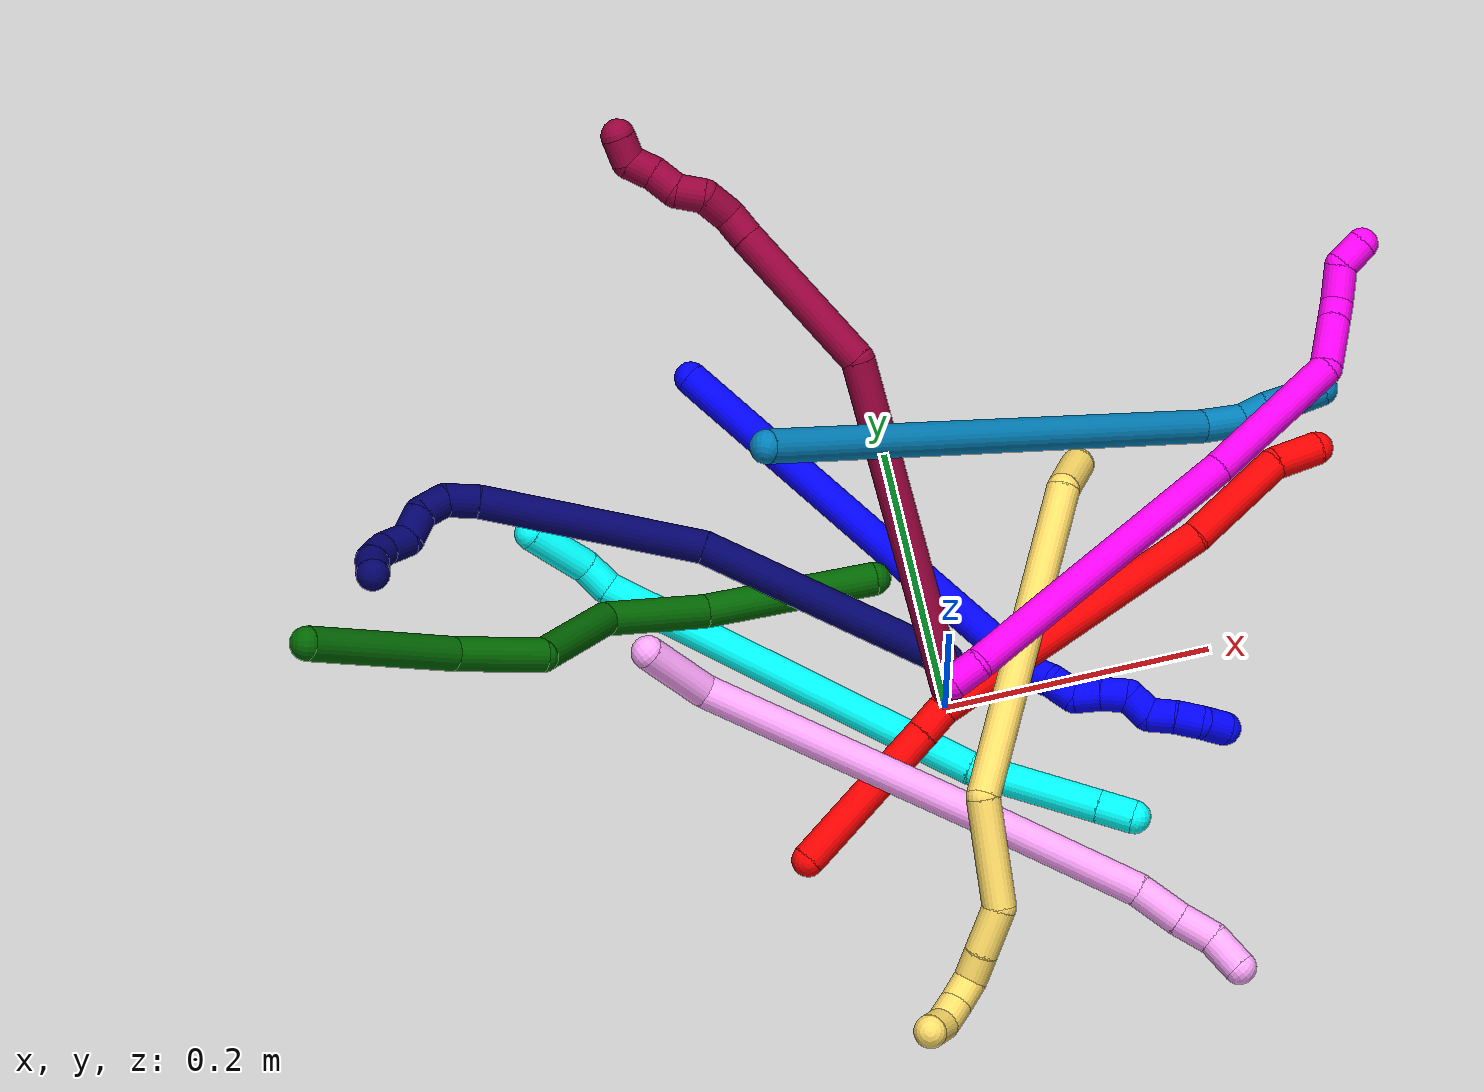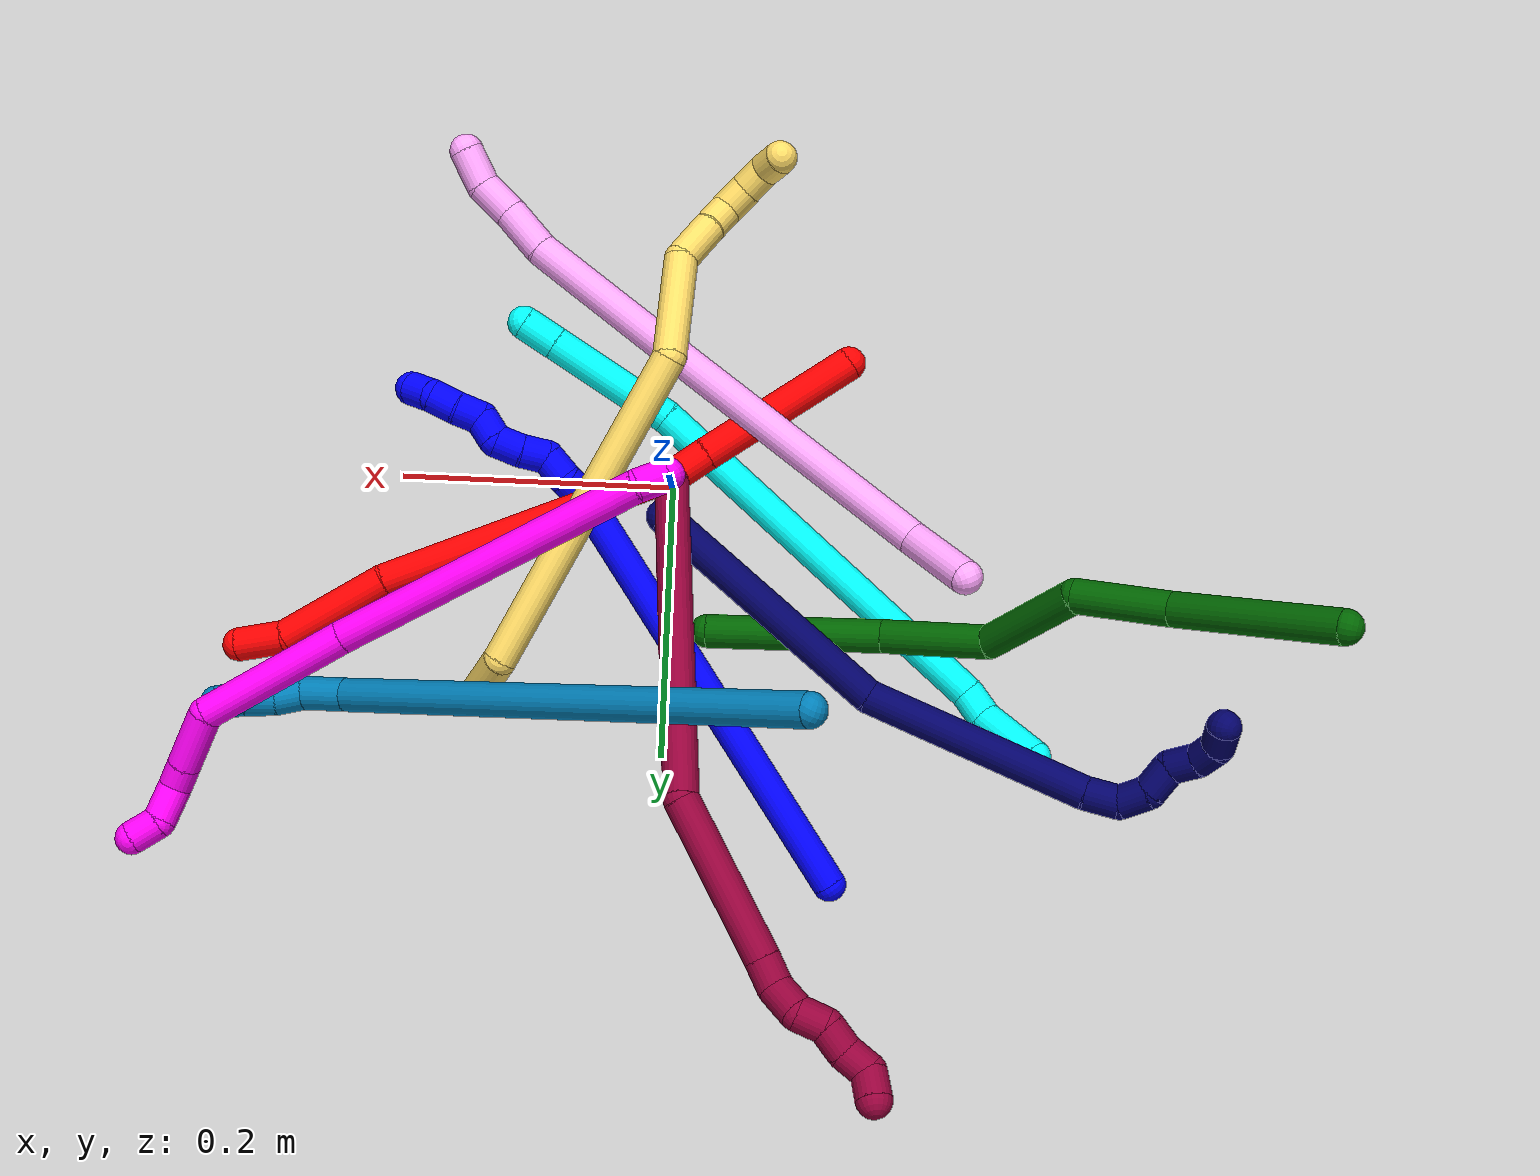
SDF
<sdf version="1.7">
 <world name="default">
  <plugin name="TubeGeneratorPlugin" filename="libtube_generator_plugin.so"/>
  <model name="photoneo_s_sensor">
   <static>1</static>
   <pose>0 0 2 1.57079 1.57079 3.14159</pose>
   <link name="link">
    <inertial><mass>0.1</mass></inertial>
    <sensor name="sensor" type="depth">
     <update_rate>30</update_rate>
     <camera>
      <horizontal_fov>1.22</horizontal_fov>
      <image><width>1920</width><height>1200</height><format>B8G8R8</format></image>
      <clip><near>0.1</near><far>4</far></clip>
      <depth_camera><output>points</output></depth_camera>
     </camera>
     <plugin name="camera_plugin" filename="libgazebo_ros_depth_camera.so">
      <baseline>0.2</baseline>
      <alwaysOn>1</alwaysOn>
      <updateRate>0.0</updateRate>
      <cameraName>camera_ir</cameraName>
      <imageTopicName>/camera/color/image_raw</imageTopicName>
      <cameraInfoTopicName>/camera/color/camera_info</cameraInfoTopicName>
      <depthImageTopicName>/camera/depth/image_raw</depthImageTopicName>
      <depthImageCameraInfoTopicName>/camera/depth/camera_info</depthImageCameraInfoTopicName>
      <pointCloudTopicName>/camera/depth/points</pointCloudTopicName>
      <frameName>fr_optical</frameName>
      <pointCloudCutoff>0.1</pointCloudCutoff>
      <pointCloudCutoffMax>2.0</pointCloudCutoffMax>
      <distortionK1>0</distortionK1>
      <distortionK2>0</distortionK2>
      <distortionK3>0</distortionK3>
      <distortionT1>0</distortionT1>
      <distortionT2>0</distortionT2>
      <CxPrime>0</CxPrime>
      <Cx>0</Cx>
      <Cy>0</Cy>
      <focalLength>0</focalLength>
      <hackBaseline>0</hackBaseline>
     </plugin>
    </sensor>
   </link>
  </model>
  <gravity>0 0 -9.8</gravity>
  <magnetic_field>6e-06 2.3e-05 -4.2e-05</magnetic_field>
  <atmosphere type="adiabatic"/>
  <physics name="default_physics" default="0" type="ode">
   <max_step_size>0.003</max_step_size>
   <real_time_factor>1</real_time_factor>
   <real_time_update_rate>1000</real_time_update_rate>
   <max_contacts>10000</max_contacts>
   <ode>
    <solver>
     <type>quick</type>
     <iters>100</iters>
     <sor>1.3</sor>
     <use_dynamic_moi_rescaling>0</use_dynamic_moi_rescaling>
    </solver>
    <constraints>
     <contact_max_correcting_vel>0</contact_max_correcting_vel>
     <contact_surface_layer>0.001</contact_surface_layer>
     <cfm>0</cfm>
     <erp>0.2</erp>
    </constraints>
   </ode>
  </physics>
  <scene><ambient>0.4 0.4 0.4 1</ambient><background>0.7 0.7 0.7 1</background><shadows>0</shadows></scene>
  <audio><device>default</device></audio>
  <spherical_coordinates>
   <surface_model>EARTH_WGS84</surface_model>
   <latitude_deg>0</latitude_deg>
   <longitude_deg>0</longitude_deg>
   <elevation>0</elevation>
   <heading_deg>0</heading_deg>
  </spherical_coordinates>
  <model name="bin">
   <static>1</static>
   <link name="bottom">
    <collision name="collision-bottom">
     <pose>0 0 -0.01 0 -0 0</pose>
     <geometry><box><size>0.8 0.6 0.02</size></box></geometry>
     <surface>
      <friction><ode><mu>100</mu><mu2>100</mu2></ode></friction>
      <contact><collide_bitmask>65535</collide_bitmask></contact>
     </surface>
    </collision>
   </link>
   <link name="west_wall">
    <collision name="collision-west_wall">
     <pose>-0.41 0 0.1 0 -0 0</pose>
     <geometry><box><size>0.02 0.6 0.2</size></box></geometry>
     <surface>
      <friction><ode><mu>100</mu><mu2>100</mu2></ode></friction>
      <contact><collide_bitmask>65535</collide_bitmask></contact>
     </surface>
    </collision>
   </link>
   <link name="east_wall">
    <collision name="collision-east_wall">
     <pose>0.41 0 0.1 0 -0 0</pose>
     <geometry><box><size>0.02 0.6 0.2</size></box></geometry>
     <surface>
      <friction><ode><mu>100</mu><mu2>100</mu2></ode></friction>
      <contact><collide_bitmask>65535</collide_bitmask></contact>
     </surface>
    </collision>
   </link>
   <link name="south_wall">
    <collision name="collision-south_wall">
     <pose>0 -0.31 0.1 0 -0 0</pose>
     <geometry><box><size>0.8 0.02 0.2</size></box></geometry>
     <surface>
      <friction><ode><mu>100</mu><mu2>100</mu2></ode></friction>
      <contact><collide_bitmask>65535</collide_bitmask></contact>
     </surface>
    </collision>
   </link>
   <link name="north_wall">
    <collision name="collision-north_wall">
     <pose>0 0.31 0.1 0 -0 0</pose>
     <geometry><box><size>0.8 0.02 0.2</size></box></geometry>
     <surface>
      <friction><ode><mu>100</mu><mu2>100</mu2></ode></friction>
      <contact><collide_bitmask>65535</collide_bitmask></contact>
     </surface>
    </collision>
   </link>
  </model>
  <model name="1">
   <static>0</static>
   <link name="1">
    <collision name="collision-cylinder-e_1_1_4">
     <pose>0.053994 -0.158262 0.025467 1.41125 0.324899 0.277464</pose>
     <geometry><cylinder><radius>0.0125</radius><length>0.338294</length></cylinder></geometry>
     <surface>
      <friction><ode><mu>1.16</mu><mu2>1.16</mu2><slip1>0</slip1><slip2>0</slip2></ode></friction>
      <contact><ode><kp>1e+06</kp><kd>1</kd><max_vel>0</max_vel><min_depth>0.001</min_depth></ode></contact>
     </surface>
    </collision>
    <visual name="visual-cylinder-e_1_1_4">
     <pose>0.053994 -0.158262 0.025467 1.41125 0.324899 0.277464</pose>
     <geometry><cylinder><radius>0.0125</radius><length>0.338294</length></cylinder></geometry>
     <material><ambient>0 0 1 1</ambient></material>
    </visual>
    <collision name="collision-cylinder-e_2_4_5">
     <pose>0.114764 -0.324826 0.049487 1.74329 0.677254 0.793318</pose>
     <geometry><cylinder><radius>0.0125</radius><length>0.021627</length></cylinder></geometry>
     <surface>
      <friction><ode><mu>1.16</mu><mu2>1.16</mu2><slip1>0</slip1><slip2>0</slip2></ode></friction>
      <contact><ode><kp>1e+06</kp><kd>1</kd><max_vel>0</max_vel><min_depth>0.001</min_depth></ode></contact>
     </surface>
    </collision>
    <visual name="visual-cylinder-e_2_4_5">
     <pose>0.114764 -0.324826 0.049487 1.74329 0.677254 0.793318</pose>
     <geometry><cylinder><radius>0.0125</radius><length>0.021627</length></cylinder></geometry>
     <material><ambient>0 0 1 1</ambient></material>
    </visual>
    <collision name="collision-cylinder-e_3_5_6">
     <pose>0.124332 -0.342738 0.048346 1.53905 0.282491 0.273775</pose>
     <geometry><cylinder><radius>0.0125</radius><length>0.020024</length></cylinder></geometry>
     <surface>
      <friction><ode><mu>1.16</mu><mu2>1.16</mu2><slip1>0</slip1><slip2>0</slip2></ode></friction>
      <contact><ode><kp>1e+06</kp><kd>1</kd><max_vel>0</max_vel><min_depth>0.001</min_depth></ode></contact>
     </surface>
    </collision>
    <visual name="visual-cylinder-e_3_5_6">
     <pose>0.124332 -0.342738 0.048346 1.53905 0.282491 0.273775</pose>
     <geometry><cylinder><radius>0.0125</radius><length>0.020024</length></cylinder></geometry>
     <material><ambient>0 0 1 1</ambient></material>
    </visual>
    <collision name="collision-cylinder-e_4_6_7">
     <pose>0.129993 -0.359819 0.042619 2.25004 0.290521 0.594157</pose>
     <geometry><cylinder><radius>0.0125</radius><length>0.020043</length></cylinder></geometry>
     <surface>
      <friction><ode><mu>1.16</mu><mu2>1.16</mu2><slip1>0</slip1><slip2>0</slip2></ode></friction>
      <contact><ode><kp>1e+06</kp><kd>1</kd><max_vel>0</max_vel><min_depth>0.001</min_depth></ode></contact>
     </surface>
    </collision>
    <visual name="visual-cylinder-e_4_6_7">
     <pose>0.129993 -0.359819 0.042619 2.25004 0.290521 0.594157</pose>
     <geometry><cylinder><radius>0.0125</radius><length>0.020043</length></cylinder></geometry>
     <material><ambient>0 0 1 1</ambient></material>
    </visual>
    <collision name="collision-cylinder-e_5_7_8">
     <pose>0.135843 -0.375632 0.031942 2.07893 0.302422 0.507367</pose>
     <geometry><cylinder><radius>0.0125</radius><length>0.020005</length></cylinder></geometry>
     <surface>
      <friction><ode><mu>1.16</mu><mu2>1.16</mu2><slip1>0</slip1><slip2>0</slip2></ode></friction>
      <contact><ode><kp>1e+06</kp><kd>1</kd><max_vel>0</max_vel><min_depth>0.001</min_depth></ode></contact>
     </surface>
    </collision>
    <visual name="visual-cylinder-e_5_7_8">
     <pose>0.135843 -0.375632 0.031942 2.07893 0.302422 0.507367</pose>
     <geometry><cylinder><radius>0.0125</radius><length>0.020005</length></cylinder></geometry>
     <material><ambient>0 0 1 1</ambient></material>
    </visual>
    <collision name="collision-cylinder-e_6_8_9">
     <pose>0.139943 -0.393727 0.029206 1.3774 0.112271 0.092448</pose>
     <geometry><cylinder><radius>0.0125</radius><length>0.020001</length></cylinder></geometry>
     <surface>
      <friction><ode><mu>1.16</mu><mu2>1.16</mu2><slip1>0</slip1><slip2>0</slip2></ode></friction>
      <contact><ode><kp>1e+06</kp><kd>1</kd><max_vel>0</max_vel><min_depth>0.001</min_depth></ode></contact>
     </surface>
    </collision>
    <visual name="visual-cylinder-e_6_8_9">
     <pose>0.139943 -0.393727 0.029206 1.3774 0.112271 0.092448</pose>
     <geometry><cylinder><radius>0.0125</radius><length>0.020001</length></cylinder></geometry>
     <material><ambient>0 0 1 1</ambient></material>
    </visual>
    <collision name="collision-cylinder-e_7_9_10">
     <pose>0.14367 -0.411992 0.02656 2.06218 0.26374 0.435818</pose>
     <geometry><cylinder><radius>0.0125</radius><length>0.020002</length></cylinder></geometry>
     <surface>
      <friction><ode><mu>1.16</mu><mu2>1.16</mu2><slip1>0</slip1><slip2>0</slip2></ode></friction>
      <contact><ode><kp>1e+06</kp><kd>1</kd><max_vel>0</max_vel><min_depth>0.001</min_depth></ode></contact>
     </surface>
    </collision>
    <visual name="visual-cylinder-e_7_9_10">
     <pose>0.14367 -0.411992 0.02656 2.06218 0.26374 0.435818</pose>
     <geometry><cylinder><radius>0.0125</radius><length>0.020002</length></cylinder></geometry>
     <material><ambient>0 0 1 1</ambient></material>
    </visual>
    <collision name="collision-cylinder-e_8_10_11">
     <pose>0.147796 -0.429738 0.018476 1.93569 0.152457 0.220967</pose>
     <geometry><cylinder><radius>0.0125</radius><length>0.020002</length></cylinder></geometry>
     <surface>
      <friction><ode><mu>1.16</mu><mu2>1.16</mu2><slip1>0</slip1><slip2>0</slip2></ode></friction>
      <contact><ode><kp>1e+06</kp><kd>1</kd><max_vel>0</max_vel><min_depth>0.001</min_depth></ode></contact>
     </surface>
    </collision>
    <visual name="visual-cylinder-e_8_10_11">
     <pose>0.147796 -0.429738 0.018476 1.93569 0.152457 0.220967</pose>
     <geometry><cylinder><radius>0.0125</radius><length>0.020002</length></cylinder></geometry>
     <material><ambient>0 0 1 1</ambient></material>
    </visual>
    <collision name="collision-cylinder-e_9_11_2">
     <pose>0.145637 -0.447881 0.012282 1.86168 -0.376614 -0.501183</pose>
     <geometry><cylinder><radius>0.0125</radius><length>0.020001</length></cylinder></geometry>
     <surface>
      <friction><ode><mu>1.16</mu><mu2>1.16</mu2><slip1>0</slip1><slip2>0</slip2></ode></friction>
      <contact><ode><kp>1e+06</kp><kd>1</kd><max_vel>0</max_vel><min_depth>0.001</min_depth></ode></contact>
     </surface>
    </collision>
    <visual name="visual-cylinder-e_9_11_2">
     <pose>0.145637 -0.447881 0.012282 1.86168 -0.376614 -0.501183</pose>
     <geometry><cylinder><radius>0.0125</radius><length>0.020001</length></cylinder></geometry>
     <material><ambient>0 0 1 1</ambient></material>
    </visual>
    <collision name="collision-sphere-2">
     <pose>0.141959 -0.45679 0.009615 0 -0 0</pose>
     <geometry><sphere><radius>0.0125</radius></sphere></geometry>
     <surface>
      <friction><ode><mu>1.16</mu><mu2>1.16</mu2><slip1>0</slip1><slip2>0</slip2></ode></friction>
      <contact><ode><kp>1e+06</kp><kd>1</kd><max_vel>0</max_vel><min_depth>0.001</min_depth></ode></contact>
     </surface>
    </collision>
    <visual name="visual-sphere-2">
     <pose>0.141959 -0.45679 0.009615 0 -0 0</pose>
     <geometry><sphere><radius>0.0125</radius></sphere></geometry>
     <material><ambient>0 0 1 1</ambient></material>
    </visual>
    <collision name="collision-sphere-11">
     <pose>0.149315 -0.438973 0.014949 0 -0 0</pose>
     <geometry><sphere><radius>0.0125</radius></sphere></geometry>
     <surface>
      <friction><ode><mu>1.16</mu><mu2>1.16</mu2><slip1>0</slip1><slip2>0</slip2></ode></friction>
      <contact><ode><kp>1e+06</kp><kd>1</kd><max_vel>0</max_vel><min_depth>0.001</min_depth></ode></contact>
     </surface>
    </collision>
    <visual name="visual-sphere-11">
     <pose>0.149315 -0.438973 0.014949 0 -0 0</pose>
     <geometry><sphere><radius>0.0125</radius></sphere></geometry>
     <material><ambient>0 0 1 1</ambient></material>
    </visual>
    <collision name="collision-sphere-10">
     <pose>0.146277 -0.420504 0.022004 0 -0 0</pose>
     <geometry><sphere><radius>0.0125</radius></sphere></geometry>
     <surface>
      <friction><ode><mu>1.16</mu><mu2>1.16</mu2><slip1>0</slip1><slip2>0</slip2></ode></friction>
      <contact><ode><kp>1e+06</kp><kd>1</kd><max_vel>0</max_vel><min_depth>0.001</min_depth></ode></contact>
     </surface>
    </collision>
    <visual name="visual-sphere-10">
     <pose>0.146277 -0.420504 0.022004 0 -0 0</pose>
     <geometry><sphere><radius>0.0125</radius></sphere></geometry>
     <material><ambient>0 0 1 1</ambient></material>
    </visual>
    <collision name="collision-sphere-9">
     <pose>0.141063 -0.403479 0.031115 0 -0 0</pose>
     <geometry><sphere><radius>0.0125</radius></sphere></geometry>
     <surface>
      <friction><ode><mu>1.16</mu><mu2>1.16</mu2><slip1>0</slip1><slip2>0</slip2></ode></friction>
      <contact><ode><kp>1e+06</kp><kd>1</kd><max_vel>0</max_vel><min_depth>0.001</min_depth></ode></contact>
     </surface>
    </collision>
    <visual name="visual-sphere-9">
     <pose>0.141063 -0.403479 0.031115 0 -0 0</pose>
     <geometry><sphere><radius>0.0125</radius></sphere></geometry>
     <material><ambient>0 0 1 1</ambient></material>
    </visual>
    <collision name="collision-sphere-4">
     <pose>0.107988 -0.316524 0.050934 0 -0 0</pose>
     <geometry><sphere><radius>0.0125</radius></sphere></geometry>
     <surface>
      <friction><ode><mu>1.16</mu><mu2>1.16</mu2><slip1>0</slip1><slip2>0</slip2></ode></friction>
      <contact><ode><kp>1e+06</kp><kd>1</kd><max_vel>0</max_vel><min_depth>0.001</min_depth></ode></contact>
     </surface>
    </collision>
    <visual name="visual-sphere-4">
     <pose>0.107988 -0.316524 0.050934 0 -0 0</pose>
     <geometry><sphere><radius>0.0125</radius></sphere></geometry>
     <material><ambient>0 0 1 1</ambient></material>
    </visual>
    <collision name="collision-sphere-1">
     <geometry><sphere><radius>0.0125</radius></sphere></geometry>
     <surface>
      <friction><ode><mu>1.16</mu><mu2>1.16</mu2><slip1>0</slip1><slip2>0</slip2></ode></friction>
      <contact><ode><kp>1e+06</kp><kd>1</kd><max_vel>0</max_vel><min_depth>0.001</min_depth></ode></contact>
     </surface>
    </collision>
    <visual name="visual-sphere-1">
     <geometry><sphere><radius>0.0125</radius></sphere></geometry>
     <material><ambient>0 0 1 1</ambient></material>
    </visual>
    <collision name="collision-sphere-8">
     <pose>0.138822 -0.383975 0.027296 0 -0 0</pose>
     <geometry><sphere><radius>0.0125</radius></sphere></geometry>
     <surface>
      <friction><ode><mu>1.16</mu><mu2>1.16</mu2><slip1>0</slip1><slip2>0</slip2></ode></friction>
      <contact><ode><kp>1e+06</kp><kd>1</kd><max_vel>0</max_vel><min_depth>0.001</min_depth></ode></contact>
     </surface>
    </collision>
    <visual name="visual-sphere-8">
     <pose>0.138822 -0.383975 0.027296 0 -0 0</pose>
     <geometry><sphere><radius>0.0125</radius></sphere></geometry>
     <material><ambient>0 0 1 1</ambient></material>
    </visual>
    <collision name="collision-sphere-5">
     <pose>0.121541 -0.333128 0.048041 0 -0 0</pose>
     <geometry><sphere><radius>0.0125</radius></sphere></geometry>
     <surface>
      <friction><ode><mu>1.16</mu><mu2>1.16</mu2><slip1>0</slip1><slip2>0</slip2></ode></friction>
      <contact><ode><kp>1e+06</kp><kd>1</kd><max_vel>0</max_vel><min_depth>0.001</min_depth></ode></contact>
     </surface>
    </collision>
    <visual name="visual-sphere-5">
     <pose>0.121541 -0.333128 0.048041 0 -0 0</pose>
     <geometry><sphere><radius>0.0125</radius></sphere></geometry>
     <material><ambient>0 0 1 1</ambient></material>
    </visual>
    <collision name="collision-sphere-6">
     <pose>0.127123 -0.352349 0.048651 0 -0 0</pose>
     <geometry><sphere><radius>0.0125</radius></sphere></geometry>
     <surface>
      <friction><ode><mu>1.16</mu><mu2>1.16</mu2><slip1>0</slip1><slip2>0</slip2></ode></friction>
      <contact><ode><kp>1e+06</kp><kd>1</kd><max_vel>0</max_vel><min_depth>0.001</min_depth></ode></contact>
     </surface>
    </collision>
    <visual name="visual-sphere-6">
     <pose>0.127123 -0.352349 0.048651 0 -0 0</pose>
     <geometry><sphere><radius>0.0125</radius></sphere></geometry>
     <material><ambient>0 0 1 1</ambient></material>
    </visual>
    <collision name="collision-sphere-7">
     <pose>0.132864 -0.36729 0.036588 0 -0 0</pose>
     <geometry><sphere><radius>0.0125</radius></sphere></geometry>
     <surface>
      <friction><ode><mu>1.16</mu><mu2>1.16</mu2><slip1>0</slip1><slip2>0</slip2></ode></friction>
      <contact><ode><kp>1e+06</kp><kd>1</kd><max_vel>0</max_vel><min_depth>0.001</min_depth></ode></contact>
     </surface>
    </collision>
    <visual name="visual-sphere-7">
     <pose>0.132864 -0.36729 0.036588 0 -0 0</pose>
     <geometry><sphere><radius>0.0125</radius></sphere></geometry>
     <material><ambient>0 0 1 1</ambient></material>
    </visual>
    <inertial>
     <pose>0.080205 -0.231646 0.027755 0 -0 0</pose>
     <mass>0.5</mass>
     <inertia>
      <ixx>0.003818</ixx>
      <ixy>0</ixy>
      <ixz>0</ixz>
      <iyy>0.001582</iyy>
      <iyz>0</iyz>
      <izz>0.002005</izz>
     </inertia>
    </inertial>
   </link>
   <pose>-0.128433 0.287725 0.011497 2.21773 -1.20721 -1.42132</pose>
  </model>
  <model name="2">
   <static>0</static>
   <link name="2">
    <collision name="collision-cylinder-e_1_1_4">
     <pose>-0.013069 -0.011242 -0.006573 2.09987 -0.787182 -1.25307</pose>
     <geometry><cylinder><radius>0.0125</radius><length>0.0369</length></cylinder></geometry>
     <surface>
      <friction><ode><mu>1.16</mu><mu2>1.16</mu2><slip1>0</slip1><slip2>0</slip2></ode></friction>
      <contact><ode><kp>1e+06</kp><kd>1</kd><max_vel>0</max_vel><min_depth>0.001</min_depth></ode></contact>
     </surface>
    </collision>
    <visual name="visual-cylinder-e_1_1_4">
     <pose>-0.013069 -0.011242 -0.006573 2.09987 -0.787182 -1.25307</pose>
     <geometry><cylinder><radius>0.0125</radius><length>0.0369</length></cylinder></geometry>
     <material><ambient>1 0 0 1</ambient></material>
    </visual>
    <collision name="collision-cylinder-e_2_4_5">
     <pose>-0.06353 -0.034182 -0.02927 2.51396 -1.08129 -2.15036</pose>
     <geometry><cylinder><radius>0.0125</radius><length>0.084734</length></cylinder></geometry>
     <surface>
      <friction><ode><mu>1.16</mu><mu2>1.16</mu2><slip1>0</slip1><slip2>0</slip2></ode></friction>
      <contact><ode><kp>1e+06</kp><kd>1</kd><max_vel>0</max_vel><min_depth>0.001</min_depth></ode></contact>
     </surface>
    </collision>
    <visual name="visual-cylinder-e_2_4_5">
     <pose>-0.06353 -0.034182 -0.02927 2.51396 -1.08129 -2.15036</pose>
     <geometry><cylinder><radius>0.0125</radius><length>0.084734</length></cylinder></geometry>
     <material><ambient>1 0 0 1</ambient></material>
    </visual>
    <collision name="collision-cylinder-e_3_5_6">
     <pose>-0.202284 -0.091948 -0.075054 2.14281 -1.07525 -1.65954</pose>
     <geometry><cylinder><radius>0.0125</radius><length>0.230446</length></cylinder></geometry>
     <surface>
      <friction><ode><mu>1.16</mu><mu2>1.16</mu2><slip1>0</slip1><slip2>0</slip2></ode></friction>
      <contact><ode><kp>1e+06</kp><kd>1</kd><max_vel>0</max_vel><min_depth>0.001</min_depth></ode></contact>
     </surface>
    </collision>
    <visual name="visual-cylinder-e_3_5_6">
     <pose>-0.202284 -0.091948 -0.075054 2.14281 -1.07525 -1.65954</pose>
     <geometry><cylinder><radius>0.0125</radius><length>0.230446</length></cylinder></geometry>
     <material><ambient>1 0 0 1</ambient></material>
    </visual>
    <collision name="collision-cylinder-e_4_6_7">
     <pose>-0.314603 -0.139613 -0.10736 2.59882 -1.29578 -2.43701</pose>
     <geometry><cylinder><radius>0.0125</radius><length>0.022768</length></cylinder></geometry>
     <surface>
      <friction><ode><mu>1.16</mu><mu2>1.16</mu2><slip1>0</slip1><slip2>0</slip2></ode></friction>
      <contact><ode><kp>1e+06</kp><kd>1</kd><max_vel>0</max_vel><min_depth>0.001</min_depth></ode></contact>
     </surface>
    </collision>
    <visual name="visual-cylinder-e_4_6_7">
     <pose>-0.314603 -0.139613 -0.10736 2.59882 -1.29578 -2.43701</pose>
     <geometry><cylinder><radius>0.0125</radius><length>0.022768</length></cylinder></geometry>
     <material><ambient>1 0 0 1</ambient></material>
    </visual>
    <collision name="collision-cylinder-e_5_7_2">
     <pose>-0.385432 -0.15159 -0.12495 2.53448 -1.27578 -2.34197</pose>
     <geometry><cylinder><radius>0.0125</radius><length>0.125152</length></cylinder></geometry>
     <surface>
      <friction><ode><mu>1.16</mu><mu2>1.16</mu2><slip1>0</slip1><slip2>0</slip2></ode></friction>
      <contact><ode><kp>1e+06</kp><kd>1</kd><max_vel>0</max_vel><min_depth>0.001</min_depth></ode></contact>
     </surface>
    </collision>
    <visual name="visual-cylinder-e_5_7_2">
     <pose>-0.385432 -0.15159 -0.12495 2.53448 -1.27578 -2.34197</pose>
     <geometry><cylinder><radius>0.0125</radius><length>0.125152</length></cylinder></geometry>
     <material><ambient>1 0 0 1</ambient></material>
    </visual>
    <collision name="collision-sphere-2">
     <pose>-0.445305 -0.16197 -0.139893 0 -0 0</pose>
     <geometry><sphere><radius>0.0125</radius></sphere></geometry>
     <surface>
      <friction><ode><mu>1.16</mu><mu2>1.16</mu2><slip1>0</slip1><slip2>0</slip2></ode></friction>
      <contact><ode><kp>1e+06</kp><kd>1</kd><max_vel>0</max_vel><min_depth>0.001</min_depth></ode></contact>
     </surface>
    </collision>
    <visual name="visual-sphere-2">
     <pose>-0.445305 -0.16197 -0.139893 0 -0 0</pose>
     <geometry><sphere><radius>0.0125</radius></sphere></geometry>
     <material><ambient>1 0 0 1</ambient></material>
    </visual>
    <collision name="collision-sphere-7">
     <pose>-0.325559 -0.14121 -0.110007 0 -0 0</pose>
     <geometry><sphere><radius>0.0125</radius></sphere></geometry>
     <surface>
      <friction><ode><mu>1.16</mu><mu2>1.16</mu2><slip1>0</slip1><slip2>0</slip2></ode></friction>
      <contact><ode><kp>1e+06</kp><kd>1</kd><max_vel>0</max_vel><min_depth>0.001</min_depth></ode></contact>
     </surface>
    </collision>
    <visual name="visual-sphere-7">
     <pose>-0.325559 -0.14121 -0.110007 0 -0 0</pose>
     <geometry><sphere><radius>0.0125</radius></sphere></geometry>
     <material><ambient>1 0 0 1</ambient></material>
    </visual>
    <collision name="collision-sphere-6">
     <pose>-0.303647 -0.138017 -0.104713 0 -0 0</pose>
     <geometry><sphere><radius>0.0125</radius></sphere></geometry>
     <surface>
      <friction><ode><mu>1.16</mu><mu2>1.16</mu2><slip1>0</slip1><slip2>0</slip2></ode></friction>
      <contact><ode><kp>1e+06</kp><kd>1</kd><max_vel>0</max_vel><min_depth>0.001</min_depth></ode></contact>
     </surface>
    </collision>
    <visual name="visual-sphere-6">
     <pose>-0.303647 -0.138017 -0.104713 0 -0 0</pose>
     <geometry><sphere><radius>0.0125</radius></sphere></geometry>
     <material><ambient>1 0 0 1</ambient></material>
    </visual>
    <collision name="collision-sphere-5">
     <pose>-0.100921 -0.04588 -0.045394 0 -0 0</pose>
     <geometry><sphere><radius>0.0125</radius></sphere></geometry>
     <surface>
      <friction><ode><mu>1.16</mu><mu2>1.16</mu2><slip1>0</slip1><slip2>0</slip2></ode></friction>
      <contact><ode><kp>1e+06</kp><kd>1</kd><max_vel>0</max_vel><min_depth>0.001</min_depth></ode></contact>
     </surface>
    </collision>
    <visual name="visual-sphere-5">
     <pose>-0.100921 -0.04588 -0.045394 0 -0 0</pose>
     <geometry><sphere><radius>0.0125</radius></sphere></geometry>
     <material><ambient>1 0 0 1</ambient></material>
    </visual>
    <collision name="collision-sphere-1">
     <geometry><sphere><radius>0.0125</radius></sphere></geometry>
     <surface>
      <friction><ode><mu>1.16</mu><mu2>1.16</mu2><slip1>0</slip1><slip2>0</slip2></ode></friction>
      <contact><ode><kp>1e+06</kp><kd>1</kd><max_vel>0</max_vel><min_depth>0.001</min_depth></ode></contact>
     </surface>
    </collision>
    <visual name="visual-sphere-1">
     <geometry><sphere><radius>0.0125</radius></sphere></geometry>
     <material><ambient>1 0 0 1</ambient></material>
    </visual>
    <collision name="collision-sphere-4">
     <pose>-0.026138 -0.022484 -0.013146 0 -0 0</pose>
     <geometry><sphere><radius>0.0125</radius></sphere></geometry>
     <surface>
      <friction><ode><mu>1.16</mu><mu2>1.16</mu2><slip1>0</slip1><slip2>0</slip2></ode></friction>
      <contact><ode><kp>1e+06</kp><kd>1</kd><max_vel>0</max_vel><min_depth>0.001</min_depth></ode></contact>
     </surface>
    </collision>
    <visual name="visual-sphere-4">
     <pose>-0.026138 -0.022484 -0.013146 0 -0 0</pose>
     <geometry><sphere><radius>0.0125</radius></sphere></geometry>
     <material><ambient>1 0 0 1</ambient></material>
    </visual>
    <inertial>
     <pose>-0.215763 -0.093302 -0.076201 0 -0 0</pose>
     <mass>0.5</mass>
     <inertia>
      <ixx>-0.000673</ixx>
      <ixy>0</ixy>
      <ixz>0</ixz>
      <iyy>0.000461</iyy>
      <iyz>0</iyz>
      <izz>0.001566</izz>
     </inertia>
    </inertial>
   </link>
   <pose>0.314262 0.12962 0.012489 -2.79589 -0.3701 0.688477</pose>
  </model>
  <model name="3">
   <static>0</static>
   <link name="3">
    <collision name="collision-cylinder-e_1_1_4">
     <pose>-0.007989 0.009735 -0.005107 -2.05388 -0.628401 0.98626</pose>
     <geometry><cylinder><radius>0.0125</radius><length>0.027179</length></cylinder></geometry>
     <surface>
      <friction><ode><mu>1.16</mu><mu2>1.16</mu2><slip1>0</slip1><slip2>0</slip2></ode></friction>
      <contact><ode><kp>1e+06</kp><kd>1</kd><max_vel>0</max_vel><min_depth>0.001</min_depth></ode></contact>
     </surface>
    </collision>
    <visual name="visual-cylinder-e_1_1_4">
     <pose>-0.007989 0.009735 -0.005107 -2.05388 -0.628401 0.98626</pose>
     <geometry><cylinder><radius>0.0125</radius><length>0.027179</length></cylinder></geometry>
     <material><ambient>0.003922 1 0.996078 1</ambient></material>
    </visual>
    <collision name="collision-cylinder-e_2_4_5">
     <pose>-0.0447 0.054974 -0.028114 -2.0378 -0.625593 0.967303</pose>
     <geometry><cylinder><radius>0.0125</radius><length>0.0981</length></cylinder></geometry>
     <surface>
      <friction><ode><mu>1.16</mu><mu2>1.16</mu2><slip1>0</slip1><slip2>0</slip2></ode></friction>
      <contact><ode><kp>1e+06</kp><kd>1</kd><max_vel>0</max_vel><min_depth>0.001</min_depth></ode></contact>
     </surface>
    </collision>
    <visual name="visual-cylinder-e_2_4_5">
     <pose>-0.0447 0.054974 -0.028114 -2.0378 -0.625593 0.967303</pose>
     <geometry><cylinder><radius>0.0125</radius><length>0.0981</length></cylinder></geometry>
     <material><ambient>0.003922 1 0.996078 1</ambient></material>
    </visual>
    <collision name="collision-cylinder-e_3_5_6">
     <pose>-0.180949 0.182521 -0.09732 -2.0793 -0.795496 1.24169</pose>
     <geometry><cylinder><radius>0.0125</radius><length>0.301106</length></cylinder></geometry>
     <surface>
      <friction><ode><mu>1.16</mu><mu2>1.16</mu2><slip1>0</slip1><slip2>0</slip2></ode></friction>
      <contact><ode><kp>1e+06</kp><kd>1</kd><max_vel>0</max_vel><min_depth>0.001</min_depth></ode></contact>
     </surface>
    </collision>
    <visual name="visual-cylinder-e_3_5_6">
     <pose>-0.180949 0.182521 -0.09732 -2.0793 -0.795496 1.24169</pose>
     <geometry><cylinder><radius>0.0125</radius><length>0.301106</length></cylinder></geometry>
     <material><ambient>0.003922 1 0.996078 1</ambient></material>
    </visual>
    <collision name="collision-cylinder-e_4_6_7">
     <pose>-0.298465 0.277001 -0.154599 -2.75436 -0.997322 2.45038</pose>
     <geometry><cylinder><radius>0.0125</radius><length>0.023784</length></cylinder></geometry>
     <surface>
      <friction><ode><mu>1.16</mu><mu2>1.16</mu2><slip1>0</slip1><slip2>0</slip2></ode></friction>
      <contact><ode><kp>1e+06</kp><kd>1</kd><max_vel>0</max_vel><min_depth>0.001</min_depth></ode></contact>
     </surface>
    </collision>
    <visual name="visual-cylinder-e_4_6_7">
     <pose>-0.298465 0.277001 -0.154599 -2.75436 -0.997322 2.45038</pose>
     <geometry><cylinder><radius>0.0125</radius><length>0.023784</length></cylinder></geometry>
     <material><ambient>0.003922 1 0.996078 1</ambient></material>
    </visual>
    <collision name="collision-cylinder-e_5_7_2">
     <pose>-0.324479 0.285065 -0.178803 -2.84219 -0.698618 2.3564</pose>
     <geometry><cylinder><radius>0.0125</radius><length>0.049831</length></cylinder></geometry>
     <surface>
      <friction><ode><mu>1.16</mu><mu2>1.16</mu2><slip1>0</slip1><slip2>0</slip2></ode></friction>
      <contact><ode><kp>1e+06</kp><kd>1</kd><max_vel>0</max_vel><min_depth>0.001</min_depth></ode></contact>
     </surface>
    </collision>
    <visual name="visual-cylinder-e_5_7_2">
     <pose>-0.324479 0.285065 -0.178803 -2.84219 -0.698618 2.3564</pose>
     <geometry><cylinder><radius>0.0125</radius><length>0.049831</length></cylinder></geometry>
     <material><ambient>0.003922 1 0.996078 1</ambient></material>
    </visual>
    <collision name="collision-sphere-2">
     <pose>-0.340504 0.290692 -0.197033 0 -0 0</pose>
     <geometry><sphere><radius>0.0125</radius></sphere></geometry>
     <surface>
      <friction><ode><mu>1.16</mu><mu2>1.16</mu2><slip1>0</slip1><slip2>0</slip2></ode></friction>
      <contact><ode><kp>1e+06</kp><kd>1</kd><max_vel>0</max_vel><min_depth>0.001</min_depth></ode></contact>
     </surface>
    </collision>
    <visual name="visual-sphere-2">
     <pose>-0.340504 0.290692 -0.197033 0 -0 0</pose>
     <geometry><sphere><radius>0.0125</radius></sphere></geometry>
     <material><ambient>0.003922 1 0.996078 1</ambient></material>
    </visual>
    <collision name="collision-sphere-7">
     <pose>-0.308455 0.279438 -0.160574 0 -0 0</pose>
     <geometry><sphere><radius>0.0125</radius></sphere></geometry>
     <surface>
      <friction><ode><mu>1.16</mu><mu2>1.16</mu2><slip1>0</slip1><slip2>0</slip2></ode></friction>
      <contact><ode><kp>1e+06</kp><kd>1</kd><max_vel>0</max_vel><min_depth>0.001</min_depth></ode></contact>
     </surface>
    </collision>
    <visual name="visual-sphere-7">
     <pose>-0.308455 0.279438 -0.160574 0 -0 0</pose>
     <geometry><sphere><radius>0.0125</radius></sphere></geometry>
     <material><ambient>0.003922 1 0.996078 1</ambient></material>
    </visual>
    <collision name="collision-sphere-6">
     <pose>-0.288476 0.274565 -0.148625 0 -0 0</pose>
     <geometry><sphere><radius>0.0125</radius></sphere></geometry>
     <surface>
      <friction><ode><mu>1.16</mu><mu2>1.16</mu2><slip1>0</slip1><slip2>0</slip2></ode></friction>
      <contact><ode><kp>1e+06</kp><kd>1</kd><max_vel>0</max_vel><min_depth>0.001</min_depth></ode></contact>
     </surface>
    </collision>
    <visual name="visual-sphere-6">
     <pose>-0.288476 0.274565 -0.148625 0 -0 0</pose>
     <geometry><sphere><radius>0.0125</radius></sphere></geometry>
     <material><ambient>0.003922 1 0.996078 1</ambient></material>
    </visual>
    <collision name="collision-sphere-5">
     <pose>-0.073423 0.090478 -0.046015 0 -0 0</pose>
     <geometry><sphere><radius>0.0125</radius></sphere></geometry>
     <surface>
      <friction><ode><mu>1.16</mu><mu2>1.16</mu2><slip1>0</slip1><slip2>0</slip2></ode></friction>
      <contact><ode><kp>1e+06</kp><kd>1</kd><max_vel>0</max_vel><min_depth>0.001</min_depth></ode></contact>
     </surface>
    </collision>
    <visual name="visual-sphere-5">
     <pose>-0.073423 0.090478 -0.046015 0 -0 0</pose>
     <geometry><sphere><radius>0.0125</radius></sphere></geometry>
     <material><ambient>0.003922 1 0.996078 1</ambient></material>
    </visual>
    <collision name="collision-sphere-1">
     <geometry><sphere><radius>0.0125</radius></sphere></geometry>
     <surface>
      <friction><ode><mu>1.16</mu><mu2>1.16</mu2><slip1>0</slip1><slip2>0</slip2></ode></friction>
      <contact><ode><kp>1e+06</kp><kd>1</kd><max_vel>0</max_vel><min_depth>0.001</min_depth></ode></contact>
     </surface>
    </collision>
    <visual name="visual-sphere-1">
     <geometry><sphere><radius>0.0125</radius></sphere></geometry>
     <material><ambient>0.003922 1 0.996078 1</ambient></material>
    </visual>
    <collision name="collision-sphere-4">
     <pose>-0.015977 0.019471 -0.010213 0 -0 0</pose>
     <geometry><sphere><radius>0.0125</radius></sphere></geometry>
     <surface>
      <friction><ode><mu>1.16</mu><mu2>1.16</mu2><slip1>0</slip1><slip2>0</slip2></ode></friction>
      <contact><ode><kp>1e+06</kp><kd>1</kd><max_vel>0</max_vel><min_depth>0.001</min_depth></ode></contact>
     </surface>
    </collision>
    <visual name="visual-sphere-4">
     <pose>-0.015977 0.019471 -0.010213 0 -0 0</pose>
     <geometry><sphere><radius>0.0125</radius></sphere></geometry>
     <material><ambient>0.003922 1 0.996078 1</ambient></material>
    </visual>
    <inertial>
     <pose>-0.16471 0.162818 -0.089575 0 -0 0</pose>
     <mass>0.5</mass>
     <inertia>
      <ixx>0.002101</ixx>
      <ixy>0</ixy>
      <ixz>0</ixz>
      <iyy>0.002619</iyy>
      <iyz>0</iyz>
      <izz>0.000214</izz>
     </inertia>
    </inertial>
   </link>
   <pose>0.114232 -0.116105 0.018968 -2.49892 0.133296 -1.46519</pose>
  </model>
  <model name="4">
   <static>0</static>
   <link name="4">
    <collision name="collision-cylinder-e_1_1_4">
     <pose>0.0289 -0.000108 0.004484 0.024081 1.41681 0.020631</pose>
     <geometry><cylinder><radius>0.0125</radius><length>0.058491</length></cylinder></geometry>
     <surface>
      <friction><ode><mu>1.16</mu><mu2>1.16</mu2><slip1>0</slip1><slip2>0</slip2></ode></friction>
      <contact><ode><kp>1e+06</kp><kd>1</kd><max_vel>0</max_vel><min_depth>0.001</min_depth></ode></contact>
     </surface>
    </collision>
    <visual name="visual-cylinder-e_1_1_4">
     <pose>0.0289 -0.000108 0.004484 0.024081 1.41681 0.020631</pose>
     <geometry><cylinder><radius>0.0125</radius><length>0.058491</length></cylinder></geometry>
     <material><ambient>1 0.65098 0.996078 1</ambient></material>
    </visual>
    <collision name="collision-cylinder-e_2_4_5">
     <pose>0.147482 -0.053424 0.056646 0.840161 0.898115 0.424024</pose>
     <geometry><cylinder><radius>0.0125</radius><length>0.229322</length></cylinder></geometry>
     <surface>
      <friction><ode><mu>1.16</mu><mu2>1.16</mu2><slip1>0</slip1><slip2>0</slip2></ode></friction>
      <contact><ode><kp>1e+06</kp><kd>1</kd><max_vel>0</max_vel><min_depth>0.001</min_depth></ode></contact>
     </surface>
    </collision>
    <visual name="visual-cylinder-e_2_4_5">
     <pose>0.147482 -0.053424 0.056646 0.840161 0.898115 0.424024</pose>
     <geometry><cylinder><radius>0.0125</radius><length>0.229322</length></cylinder></geometry>
     <material><ambient>1 0.65098 0.996078 1</ambient></material>
    </visual>
    <collision name="collision-cylinder-e_3_5_6">
     <pose>0.284481 -0.132956 0.127988 0.838559 0.928519 0.439192</pose>
     <geometry><cylinder><radius>0.0125</radius><length>0.118184</length></cylinder></geometry>
     <surface>
      <friction><ode><mu>1.16</mu><mu2>1.16</mu2><slip1>0</slip1><slip2>0</slip2></ode></friction>
      <contact><ode><kp>1e+06</kp><kd>1</kd><max_vel>0</max_vel><min_depth>0.001</min_depth></ode></contact>
     </surface>
    </collision>
    <visual name="visual-cylinder-e_3_5_6">
     <pose>0.284481 -0.132956 0.127988 0.838559 0.928519 0.439192</pose>
     <geometry><cylinder><radius>0.0125</radius><length>0.118184</length></cylinder></geometry>
     <material><ambient>1 0.65098 0.996078 1</ambient></material>
    </visual>
    <collision name="collision-cylinder-e_4_6_7">
     <pose>0.346358 -0.169391 0.155986 1.1659 0.923772 0.634331</pose>
     <geometry><cylinder><radius>0.0125</radius><length>0.036498</length></cylinder></geometry>
     <surface>
      <friction><ode><mu>1.16</mu><mu2>1.16</mu2><slip1>0</slip1><slip2>0</slip2></ode></friction>
      <contact><ode><kp>1e+06</kp><kd>1</kd><max_vel>0</max_vel><min_depth>0.001</min_depth></ode></contact>
     </surface>
    </collision>
    <visual name="visual-cylinder-e_4_6_7">
     <pose>0.346358 -0.169391 0.155986 1.1659 0.923772 0.634331</pose>
     <geometry><cylinder><radius>0.0125</radius><length>0.036498</length></cylinder></geometry>
     <material><ambient>1 0.65098 0.996078 1</ambient></material>
    </visual>
    <collision name="collision-cylinder-e_5_7_8">
     <pose>0.371775 -0.187572 0.165174 1.02915 0.856239 0.505006</pose>
     <geometry><cylinder><radius>0.0125</radius><length>0.028743</length></cylinder></geometry>
     <surface>
      <friction><ode><mu>1.16</mu><mu2>1.16</mu2><slip1>0</slip1><slip2>0</slip2></ode></friction>
      <contact><ode><kp>1e+06</kp><kd>1</kd><max_vel>0</max_vel><min_depth>0.001</min_depth></ode></contact>
     </surface>
    </collision>
    <visual name="visual-cylinder-e_5_7_8">
     <pose>0.371775 -0.187572 0.165174 1.02915 0.856239 0.505006</pose>
     <geometry><cylinder><radius>0.0125</radius><length>0.028743</length></cylinder></geometry>
     <material><ambient>1 0.65098 0.996078 1</ambient></material>
    </visual>
    <collision name="collision-cylinder-e_6_8_2">
     <pose>0.392064 -0.206472 0.170756 1.50381 0.715387 0.672522</pose>
     <geometry><cylinder><radius>0.0125</radius><length>0.028762</length></cylinder></geometry>
     <surface>
      <friction><ode><mu>1.16</mu><mu2>1.16</mu2><slip1>0</slip1><slip2>0</slip2></ode></friction>
      <contact><ode><kp>1e+06</kp><kd>1</kd><max_vel>0</max_vel><min_depth>0.001</min_depth></ode></contact>
     </surface>
    </collision>
    <visual name="visual-cylinder-e_6_8_2">
     <pose>0.392064 -0.206472 0.170756 1.50381 0.715387 0.672522</pose>
     <geometry><cylinder><radius>0.0125</radius><length>0.028762</length></cylinder></geometry>
     <material><ambient>1 0.65098 0.996078 1</ambient></material>
    </visual>
    <collision name="collision-sphere-2">
     <pose>0.401496 -0.217303 0.171483 0 -0 0</pose>
     <geometry><sphere><radius>0.0125</radius></sphere></geometry>
     <surface>
      <friction><ode><mu>1.16</mu><mu2>1.16</mu2><slip1>0</slip1><slip2>0</slip2></ode></friction>
      <contact><ode><kp>1e+06</kp><kd>1</kd><max_vel>0</max_vel><min_depth>0.001</min_depth></ode></contact>
     </surface>
    </collision>
    <visual name="visual-sphere-2">
     <pose>0.401496 -0.217303 0.171483 0 -0 0</pose>
     <geometry><sphere><radius>0.0125</radius></sphere></geometry>
     <material><ambient>1 0.65098 0.996078 1</ambient></material>
    </visual>
    <collision name="collision-sphere-4">
     <pose>0.057799 -0.000216 0.008969 0 -0 0</pose>
     <geometry><sphere><radius>0.0125</radius></sphere></geometry>
     <surface>
      <friction><ode><mu>1.16</mu><mu2>1.16</mu2><slip1>0</slip1><slip2>0</slip2></ode></friction>
      <contact><ode><kp>1e+06</kp><kd>1</kd><max_vel>0</max_vel><min_depth>0.001</min_depth></ode></contact>
     </surface>
    </collision>
    <visual name="visual-sphere-4">
     <pose>0.057799 -0.000216 0.008969 0 -0 0</pose>
     <geometry><sphere><radius>0.0125</radius></sphere></geometry>
     <material><ambient>1 0.65098 0.996078 1</ambient></material>
    </visual>
    <collision name="collision-sphere-1">
     <geometry><sphere><radius>0.0125</radius></sphere></geometry>
     <surface>
      <friction><ode><mu>1.16</mu><mu2>1.16</mu2><slip1>0</slip1><slip2>0</slip2></ode></friction>
      <contact><ode><kp>1e+06</kp><kd>1</kd><max_vel>0</max_vel><min_depth>0.001</min_depth></ode></contact>
     </surface>
    </collision>
    <visual name="visual-sphere-1">
     <geometry><sphere><radius>0.0125</radius></sphere></geometry>
     <material><ambient>1 0.65098 0.996078 1</ambient></material>
    </visual>
    <collision name="collision-sphere-8">
     <pose>0.382631 -0.195641 0.17003 0 -0 0</pose>
     <geometry><sphere><radius>0.0125</radius></sphere></geometry>
     <surface>
      <friction><ode><mu>1.16</mu><mu2>1.16</mu2><slip1>0</slip1><slip2>0</slip2></ode></friction>
      <contact><ode><kp>1e+06</kp><kd>1</kd><max_vel>0</max_vel><min_depth>0.001</min_depth></ode></contact>
     </surface>
    </collision>
    <visual name="visual-sphere-8">
     <pose>0.382631 -0.195641 0.17003 0 -0 0</pose>
     <geometry><sphere><radius>0.0125</radius></sphere></geometry>
     <material><ambient>1 0.65098 0.996078 1</ambient></material>
    </visual>
    <collision name="collision-sphere-5">
     <pose>0.237164 -0.106631 0.104324 0 -0 0</pose>
     <geometry><sphere><radius>0.0125</radius></sphere></geometry>
     <surface>
      <friction><ode><mu>1.16</mu><mu2>1.16</mu2><slip1>0</slip1><slip2>0</slip2></ode></friction>
      <contact><ode><kp>1e+06</kp><kd>1</kd><max_vel>0</max_vel><min_depth>0.001</min_depth></ode></contact>
     </surface>
    </collision>
    <visual name="visual-sphere-5">
     <pose>0.237164 -0.106631 0.104324 0 -0 0</pose>
     <geometry><sphere><radius>0.0125</radius></sphere></geometry>
     <material><ambient>1 0.65098 0.996078 1</ambient></material>
    </visual>
    <collision name="collision-sphere-6">
     <pose>0.331798 -0.15928 0.151652 0 -0 0</pose>
     <geometry><sphere><radius>0.0125</radius></sphere></geometry>
     <surface>
      <friction><ode><mu>1.16</mu><mu2>1.16</mu2><slip1>0</slip1><slip2>0</slip2></ode></friction>
      <contact><ode><kp>1e+06</kp><kd>1</kd><max_vel>0</max_vel><min_depth>0.001</min_depth></ode></contact>
     </surface>
    </collision>
    <visual name="visual-sphere-6">
     <pose>0.331798 -0.15928 0.151652 0 -0 0</pose>
     <geometry><sphere><radius>0.0125</radius></sphere></geometry>
     <material><ambient>1 0.65098 0.996078 1</ambient></material>
    </visual>
    <collision name="collision-sphere-7">
     <pose>0.360919 -0.179502 0.160319 0 -0 0</pose>
     <geometry><sphere><radius>0.0125</radius></sphere></geometry>
     <surface>
      <friction><ode><mu>1.16</mu><mu2>1.16</mu2><slip1>0</slip1><slip2>0</slip2></ode></friction>
      <contact><ode><kp>1e+06</kp><kd>1</kd><max_vel>0</max_vel><min_depth>0.001</min_depth></ode></contact>
     </surface>
    </collision>
    <visual name="visual-sphere-7">
     <pose>0.360919 -0.179502 0.160319 0 -0 0</pose>
     <geometry><sphere><radius>0.0125</radius></sphere></geometry>
     <material><ambient>1 0.65098 0.996078 1</ambient></material>
    </visual>
    <inertial>
     <pose>0.207472 -0.090966 0.087461 0 -0 0</pose>
     <mass>0.5</mass>
     <inertia>
      <ixx>0.000994</ixx>
      <ixy>0</ixy>
      <ixz>0</ixz>
      <iyy>0.001292</iyy>
      <iyz>0</iyz>
      <izz>-0.00038</izz>
     </inertia>
    </inertial>
   </link>
   <pose>-0.207887 0.057586 0.117597 -1.18535 0.803315 -0.841209</pose>
  </model>
  <model name="5">
   <static>0</static>
   <link name="5">
    <collision name="collision-cylinder-e_1_1_4">
     <pose>-0.009506 -0.006628 0.020079 0.318833 -0.422486 -0.068929</pose>
     <geometry><cylinder><radius>0.0125</radius><length>0.046366</length></cylinder></geometry>
     <surface>
      <friction><ode><mu>1.16</mu><mu2>1.16</mu2><slip1>0</slip1><slip2>0</slip2></ode></friction>
      <contact><ode><kp>1e+06</kp><kd>1</kd><max_vel>0</max_vel><min_depth>0.001</min_depth></ode></contact>
     </surface>
    </collision>
    <visual name="visual-cylinder-e_1_1_4">
     <pose>-0.009506 -0.006628 0.020079 0.318833 -0.422486 -0.068929</pose>
     <geometry><cylinder><radius>0.0125</radius><length>0.046366</length></cylinder></geometry>
     <material><ambient>1 0.858824 0.4 1</ambient></material>
    </visual>
    <collision name="collision-cylinder-e_2_4_5">
     <pose>-0.096998 -0.101756 0.082888 1.12099 -0.670799 -0.430763</pose>
     <geometry><cylinder><radius>0.0125</radius><length>0.250918</length></cylinder></geometry>
     <surface>
      <friction><ode><mu>1.16</mu><mu2>1.16</mu2><slip1>0</slip1><slip2>0</slip2></ode></friction>
      <contact><ode><kp>1e+06</kp><kd>1</kd><max_vel>0</max_vel><min_depth>0.001</min_depth></ode></contact>
     </surface>
    </collision>
    <visual name="visual-cylinder-e_2_4_5">
     <pose>-0.096998 -0.101756 0.082888 1.12099 -0.670799 -0.430763</pose>
     <geometry><cylinder><radius>0.0125</radius><length>0.250918</length></cylinder></geometry>
     <material><ambient>1 0.858824 0.4 1</ambient></material>
    </visual>
    <collision name="collision-cylinder-e_3_5_6">
     <pose>-0.187768 -0.228343 0.118405 1.75794 -0.318534 -0.383043</pose>
     <geometry><cylinder><radius>0.0125</radius><length>0.081635</length></cylinder></geometry>
     <surface>
      <friction><ode><mu>1.16</mu><mu2>1.16</mu2><slip1>0</slip1><slip2>0</slip2></ode></friction>
      <contact><ode><kp>1e+06</kp><kd>1</kd><max_vel>0</max_vel><min_depth>0.001</min_depth></ode></contact>
     </surface>
    </collision>
    <visual name="visual-cylinder-e_3_5_6">
     <pose>-0.187768 -0.228343 0.118405 1.75794 -0.318534 -0.383043</pose>
     <geometry><cylinder><radius>0.0125</radius><length>0.081635</length></cylinder></geometry>
     <material><ambient>1 0.858824 0.4 1</ambient></material>
    </visual>
    <collision name="collision-cylinder-e_4_6_7">
     <pose>-0.213828 -0.278036 0.106691 1.94082 -0.817599 -1.12822</pose>
     <geometry><cylinder><radius>0.0125</radius><length>0.0364</length></cylinder></geometry>
     <surface>
      <friction><ode><mu>1.16</mu><mu2>1.16</mu2><slip1>0</slip1><slip2>0</slip2></ode></friction>
      <contact><ode><kp>1e+06</kp><kd>1</kd><max_vel>0</max_vel><min_depth>0.001</min_depth></ode></contact>
     </surface>
    </collision>
    <visual name="visual-cylinder-e_4_6_7">
     <pose>-0.213828 -0.278036 0.106691 1.94082 -0.817599 -1.12822</pose>
     <geometry><cylinder><radius>0.0125</radius><length>0.0364</length></cylinder></geometry>
     <material><ambient>1 0.858824 0.4 1</ambient></material>
    </visual>
    <collision name="collision-cylinder-e_5_7_8">
     <pose>-0.235218 -0.296733 0.098343 2.06776 -0.788212 -1.21963</pose>
     <geometry><cylinder><radius>0.0125</radius><length>0.022882</length></cylinder></geometry>
     <surface>
      <friction><ode><mu>1.16</mu><mu2>1.16</mu2><slip1>0</slip1><slip2>0</slip2></ode></friction>
      <contact><ode><kp>1e+06</kp><kd>1</kd><max_vel>0</max_vel><min_depth>0.001</min_depth></ode></contact>
     </surface>
    </collision>
    <visual name="visual-cylinder-e_5_7_8">
     <pose>-0.235218 -0.296733 0.098343 2.06776 -0.788212 -1.21963</pose>
     <geometry><cylinder><radius>0.0125</radius><length>0.022882</length></cylinder></geometry>
     <material><ambient>1 0.858824 0.4 1</ambient></material>
    </visual>
    <collision name="collision-cylinder-e_6_8_9">
     <pose>-0.251827 -0.309067 0.098145 0.962949 -0.926226 -0.510411</pose>
     <geometry><cylinder><radius>0.0125</radius><length>0.02126</length></cylinder></geometry>
     <surface>
      <friction><ode><mu>1.16</mu><mu2>1.16</mu2><slip1>0</slip1><slip2>0</slip2></ode></friction>
      <contact><ode><kp>1e+06</kp><kd>1</kd><max_vel>0</max_vel><min_depth>0.001</min_depth></ode></contact>
     </surface>
    </collision>
    <visual name="visual-cylinder-e_6_8_9">
     <pose>-0.251827 -0.309067 0.098145 0.962949 -0.926226 -0.510411</pose>
     <geometry><cylinder><radius>0.0125</radius><length>0.02126</length></cylinder></geometry>
     <material><ambient>1 0.858824 0.4 1</ambient></material>
    </visual>
    <collision name="collision-cylinder-e_7_9_10">
     <pose>-0.267804 -0.318566 0.107137 0.67247 -0.830591 -0.305818</pose>
     <geometry><cylinder><radius>0.0125</radius><length>0.020259</length></cylinder></geometry>
     <surface>
      <friction><ode><mu>1.16</mu><mu2>1.16</mu2><slip1>0</slip1><slip2>0</slip2></ode></friction>
      <contact><ode><kp>1e+06</kp><kd>1</kd><max_vel>0</max_vel><min_depth>0.001</min_depth></ode></contact>
     </surface>
    </collision>
    <visual name="visual-cylinder-e_7_9_10">
     <pose>-0.267804 -0.318566 0.107137 0.67247 -0.830591 -0.305818</pose>
     <geometry><cylinder><radius>0.0125</radius><length>0.020259</length></cylinder></geometry>
     <material><ambient>1 0.858824 0.4 1</ambient></material>
    </visual>
    <collision name="collision-cylinder-e_8_10_2">
     <pose>-0.280024 -0.32311 0.12144 0.032182 -0.486625 -0.007989</pose>
     <geometry><cylinder><radius>0.0125</radius><length>0.02028</length></cylinder></geometry>
     <surface>
      <friction><ode><mu>1.16</mu><mu2>1.16</mu2><slip1>0</slip1><slip2>0</slip2></ode></friction>
      <contact><ode><kp>1e+06</kp><kd>1</kd><max_vel>0</max_vel><min_depth>0.001</min_depth></ode></contact>
     </surface>
    </collision>
    <visual name="visual-cylinder-e_8_10_2">
     <pose>-0.280024 -0.32311 0.12144 0.032182 -0.486625 -0.007989</pose>
     <geometry><cylinder><radius>0.0125</radius><length>0.02028</length></cylinder></geometry>
     <material><ambient>1 0.858824 0.4 1</ambient></material>
    </visual>
    <collision name="collision-sphere-2">
     <pose>-0.284766 -0.323398 0.130398 0 -0 0</pose>
     <geometry><sphere><radius>0.0125</radius></sphere></geometry>
     <surface>
      <friction><ode><mu>1.16</mu><mu2>1.16</mu2><slip1>0</slip1><slip2>0</slip2></ode></friction>
      <contact><ode><kp>1e+06</kp><kd>1</kd><max_vel>0</max_vel><min_depth>0.001</min_depth></ode></contact>
     </surface>
    </collision>
    <visual name="visual-sphere-2">
     <pose>-0.284766 -0.323398 0.130398 0 -0 0</pose>
     <geometry><sphere><radius>0.0125</radius></sphere></geometry>
     <material><ambient>1 0.858824 0.4 1</ambient></material>
    </visual>
    <collision name="collision-sphere-10">
     <pose>-0.275282 -0.322821 0.112481 0 -0 0</pose>
     <geometry><sphere><radius>0.0125</radius></sphere></geometry>
     <surface>
      <friction><ode><mu>1.16</mu><mu2>1.16</mu2><slip1>0</slip1><slip2>0</slip2></ode></friction>
      <contact><ode><kp>1e+06</kp><kd>1</kd><max_vel>0</max_vel><min_depth>0.001</min_depth></ode></contact>
     </surface>
    </collision>
    <visual name="visual-sphere-10">
     <pose>-0.275282 -0.322821 0.112481 0 -0 0</pose>
     <geometry><sphere><radius>0.0125</radius></sphere></geometry>
     <material><ambient>1 0.858824 0.4 1</ambient></material>
    </visual>
    <collision name="collision-sphere-9">
     <pose>-0.260325 -0.31431 0.101793 0 -0 0</pose>
     <geometry><sphere><radius>0.0125</radius></sphere></geometry>
     <surface>
      <friction><ode><mu>1.16</mu><mu2>1.16</mu2><slip1>0</slip1><slip2>0</slip2></ode></friction>
      <contact><ode><kp>1e+06</kp><kd>1</kd><max_vel>0</max_vel><min_depth>0.001</min_depth></ode></contact>
     </surface>
    </collision>
    <visual name="visual-sphere-9">
     <pose>-0.260325 -0.31431 0.101793 0 -0 0</pose>
     <geometry><sphere><radius>0.0125</radius></sphere></geometry>
     <material><ambient>1 0.858824 0.4 1</ambient></material>
    </visual>
    <collision name="collision-sphere-4">
     <pose>-0.019012 -0.013256 0.040158 0 -0 0</pose>
     <geometry><sphere><radius>0.0125</radius></sphere></geometry>
     <surface>
      <friction><ode><mu>1.16</mu><mu2>1.16</mu2><slip1>0</slip1><slip2>0</slip2></ode></friction>
      <contact><ode><kp>1e+06</kp><kd>1</kd><max_vel>0</max_vel><min_depth>0.001</min_depth></ode></contact>
     </surface>
    </collision>
    <visual name="visual-sphere-4">
     <pose>-0.019012 -0.013256 0.040158 0 -0 0</pose>
     <geometry><sphere><radius>0.0125</radius></sphere></geometry>
     <material><ambient>1 0.858824 0.4 1</ambient></material>
    </visual>
    <collision name="collision-sphere-1">
     <geometry><sphere><radius>0.0125</radius></sphere></geometry>
     <surface>
      <friction><ode><mu>1.16</mu><mu2>1.16</mu2><slip1>0</slip1><slip2>0</slip2></ode></friction>
      <contact><ode><kp>1e+06</kp><kd>1</kd><max_vel>0</max_vel><min_depth>0.001</min_depth></ode></contact>
     </surface>
    </collision>
    <visual name="visual-sphere-1">
     <geometry><sphere><radius>0.0125</radius></sphere></geometry>
     <material><ambient>1 0.858824 0.4 1</ambient></material>
    </visual>
    <collision name="collision-sphere-8">
     <pose>-0.24333 -0.303824 0.094497 0 -0 0</pose>
     <geometry><sphere><radius>0.0125</radius></sphere></geometry>
     <surface>
      <friction><ode><mu>1.16</mu><mu2>1.16</mu2><slip1>0</slip1><slip2>0</slip2></ode></friction>
      <contact><ode><kp>1e+06</kp><kd>1</kd><max_vel>0</max_vel><min_depth>0.001</min_depth></ode></contact>
     </surface>
    </collision>
    <visual name="visual-sphere-8">
     <pose>-0.24333 -0.303824 0.094497 0 -0 0</pose>
     <geometry><sphere><radius>0.0125</radius></sphere></geometry>
     <material><ambient>1 0.858824 0.4 1</ambient></material>
    </visual>
    <collision name="collision-sphere-5">
     <pose>-0.174985 -0.190255 0.125617 0 -0 0</pose>
     <geometry><sphere><radius>0.0125</radius></sphere></geometry>
     <surface>
      <friction><ode><mu>1.16</mu><mu2>1.16</mu2><slip1>0</slip1><slip2>0</slip2></ode></friction>
      <contact><ode><kp>1e+06</kp><kd>1</kd><max_vel>0</max_vel><min_depth>0.001</min_depth></ode></contact>
     </surface>
    </collision>
    <visual name="visual-sphere-5">
     <pose>-0.174985 -0.190255 0.125617 0 -0 0</pose>
     <geometry><sphere><radius>0.0125</radius></sphere></geometry>
     <material><ambient>1 0.858824 0.4 1</ambient></material>
    </visual>
    <collision name="collision-sphere-6">
     <pose>-0.200551 -0.26643 0.111193 0 -0 0</pose>
     <geometry><sphere><radius>0.0125</radius></sphere></geometry>
     <surface>
      <friction><ode><mu>1.16</mu><mu2>1.16</mu2><slip1>0</slip1><slip2>0</slip2></ode></friction>
      <contact><ode><kp>1e+06</kp><kd>1</kd><max_vel>0</max_vel><min_depth>0.001</min_depth></ode></contact>
     </surface>
    </collision>
    <visual name="visual-sphere-6">
     <pose>-0.200551 -0.26643 0.111193 0 -0 0</pose>
     <geometry><sphere><radius>0.0125</radius></sphere></geometry>
     <material><ambient>1 0.858824 0.4 1</ambient></material>
    </visual>
    <collision name="collision-sphere-7">
     <pose>-0.227105 -0.289641 0.102189 0 -0 0</pose>
     <geometry><sphere><radius>0.0125</radius></sphere></geometry>
     <surface>
      <friction><ode><mu>1.16</mu><mu2>1.16</mu2><slip1>0</slip1><slip2>0</slip2></ode></friction>
      <contact><ode><kp>1e+06</kp><kd>1</kd><max_vel>0</max_vel><min_depth>0.001</min_depth></ode></contact>
     </surface>
    </collision>
    <visual name="visual-sphere-7">
     <pose>-0.227105 -0.289641 0.102189 0 -0 0</pose>
     <geometry><sphere><radius>0.0125</radius></sphere></geometry>
     <material><ambient>1 0.858824 0.4 1</ambient></material>
    </visual>
    <inertial>
     <pose>-0.139463 -0.161936 0.088497 0 -0 0</pose>
     <mass>0.5</mass>
     <inertia>
      <ixx>0.000522</ixx>
      <ixy>0</ixy>
      <ixz>0</ixz>
      <iyy>0.000366</iyy>
      <iyz>0</iyz>
      <izz>0.001852</izz>
     </inertia>
    </inertial>
   </link>
   <pose>0.137649 0.157387 0.01149 0.198559 -0.12827 0.228257</pose>
  </model>
  <model name="6">
   <static>0</static>
   <link name="6">
    <collision name="collision-cylinder-e_1_1_4">
     <pose>-0.011382 0.008931 0.063381 -0.139993 -0.175977 0.01237</pose>
     <geometry><cylinder><radius>0.0125</radius><length>0.130022</length></cylinder></geometry>
     <surface>
      <friction><ode><mu>1.16</mu><mu2>1.16</mu2><slip1>0</slip1><slip2>0</slip2></ode></friction>
      <contact><ode><kp>1e+06</kp><kd>1</kd><max_vel>0</max_vel><min_depth>0.001</min_depth></ode></contact>
     </surface>
    </collision>
    <visual name="visual-cylinder-e_1_1_4">
     <pose>-0.011382 0.008931 0.063381 -0.139993 -0.175977 0.01237</pose>
     <geometry><cylinder><radius>0.0125</radius><length>0.130022</length></cylinder></geometry>
     <material><ambient>0 0.392157 0.003922 1</ambient></material>
    </visual>
    <collision name="collision-cylinder-e_2_4_5">
     <pose>-0.034112 0.011921 0.165668 0.151547 -0.280728 -0.021453</pose>
     <geometry><cylinder><radius>0.0125</radius><length>0.081923</length></cylinder></geometry>
     <surface>
      <friction><ode><mu>1.16</mu><mu2>1.16</mu2><slip1>0</slip1><slip2>0</slip2></ode></friction>
      <contact><ode><kp>1e+06</kp><kd>1</kd><max_vel>0</max_vel><min_depth>0.001</min_depth></ode></contact>
     </surface>
    </collision>
    <visual name="visual-cylinder-e_2_4_5">
     <pose>-0.034112 0.011921 0.165668 0.151547 -0.280728 -0.021453</pose>
     <geometry><cylinder><radius>0.0125</radius><length>0.081923</length></cylinder></geometry>
     <material><ambient>0 0.392157 0.003922 1</ambient></material>
    </visual>
    <collision name="collision-cylinder-e_3_5_6">
     <pose>-0.078479 -0.009034 0.231923 0.502043 -0.813764 -0.220114</pose>
     <geometry><cylinder><radius>0.0125</radius><length>0.090852</length></cylinder></geometry>
     <surface>
      <friction><ode><mu>1.16</mu><mu2>1.16</mu2><slip1>0</slip1><slip2>0</slip2></ode></friction>
      <contact><ode><kp>1e+06</kp><kd>1</kd><max_vel>0</max_vel><min_depth>0.001</min_depth></ode></contact>
     </surface>
    </collision>
    <visual name="visual-cylinder-e_3_5_6">
     <pose>-0.078479 -0.009034 0.231923 0.502043 -0.813764 -0.220114</pose>
     <geometry><cylinder><radius>0.0125</radius><length>0.090852</length></cylinder></geometry>
     <material><ambient>0 0.392157 0.003922 1</ambient></material>
    </visual>
    <collision name="collision-cylinder-e_4_6_7">
     <pose>-0.118682 -0.030819 0.292989 0.198209 -0.205903 -0.020545</pose>
     <geometry><cylinder><radius>0.0125</radius><length>0.07027</length></cylinder></geometry>
     <surface>
      <friction><ode><mu>1.16</mu><mu2>1.16</mu2><slip1>0</slip1><slip2>0</slip2></ode></friction>
      <contact><ode><kp>1e+06</kp><kd>1</kd><max_vel>0</max_vel><min_depth>0.001</min_depth></ode></contact>
     </surface>
    </collision>
    <visual name="visual-cylinder-e_4_6_7">
     <pose>-0.118682 -0.030819 0.292989 0.198209 -0.205903 -0.020545</pose>
     <geometry><cylinder><radius>0.0125</radius><length>0.07027</length></cylinder></geometry>
     <material><ambient>0 0.392157 0.003922 1</ambient></material>
    </visual>
    <collision name="collision-cylinder-e_5_7_2">
     <pose>-0.145573 -0.061412 0.382136 0.40591 -0.315742 -0.065498</pose>
     <geometry><cylinder><radius>0.0125</radius><length>0.126933</length></cylinder></geometry>
     <surface>
      <friction><ode><mu>1.16</mu><mu2>1.16</mu2><slip1>0</slip1><slip2>0</slip2></ode></friction>
      <contact><ode><kp>1e+06</kp><kd>1</kd><max_vel>0</max_vel><min_depth>0.001</min_depth></ode></contact>
     </surface>
    </collision>
    <visual name="visual-cylinder-e_5_7_2">
     <pose>-0.145573 -0.061412 0.382136 0.40591 -0.315742 -0.065498</pose>
     <geometry><cylinder><radius>0.0125</radius><length>0.126933</length></cylinder></geometry>
     <material><ambient>0 0.392157 0.003922 1</ambient></material>
    </visual>
    <collision name="collision-sphere-2">
     <pose>-0.165281 -0.085234 0.437563 0 -0 0</pose>
     <geometry><sphere><radius>0.0125</radius></sphere></geometry>
     <surface>
      <friction><ode><mu>1.16</mu><mu2>1.16</mu2><slip1>0</slip1><slip2>0</slip2></ode></friction>
      <contact><ode><kp>1e+06</kp><kd>1</kd><max_vel>0</max_vel><min_depth>0.001</min_depth></ode></contact>
     </surface>
    </collision>
    <visual name="visual-sphere-2">
     <pose>-0.165281 -0.085234 0.437563 0 -0 0</pose>
     <geometry><sphere><radius>0.0125</radius></sphere></geometry>
     <material><ambient>0 0.392157 0.003922 1</ambient></material>
    </visual>
    <collision name="collision-sphere-7">
     <pose>-0.125865 -0.037591 0.326709 0 -0 0</pose>
     <geometry><sphere><radius>0.0125</radius></sphere></geometry>
     <surface>
      <friction><ode><mu>1.16</mu><mu2>1.16</mu2><slip1>0</slip1><slip2>0</slip2></ode></friction>
      <contact><ode><kp>1e+06</kp><kd>1</kd><max_vel>0</max_vel><min_depth>0.001</min_depth></ode></contact>
     </surface>
    </collision>
    <visual name="visual-sphere-7">
     <pose>-0.125865 -0.037591 0.326709 0 -0 0</pose>
     <geometry><sphere><radius>0.0125</radius></sphere></geometry>
     <material><ambient>0 0.392157 0.003922 1</ambient></material>
    </visual>
    <collision name="collision-sphere-6">
     <pose>-0.111498 -0.024046 0.25927 0 -0 0</pose>
     <geometry><sphere><radius>0.0125</radius></sphere></geometry>
     <surface>
      <friction><ode><mu>1.16</mu><mu2>1.16</mu2><slip1>0</slip1><slip2>0</slip2></ode></friction>
      <contact><ode><kp>1e+06</kp><kd>1</kd><max_vel>0</max_vel><min_depth>0.001</min_depth></ode></contact>
     </surface>
    </collision>
    <visual name="visual-sphere-6">
     <pose>-0.111498 -0.024046 0.25927 0 -0 0</pose>
     <geometry><sphere><radius>0.0125</radius></sphere></geometry>
     <material><ambient>0 0.392157 0.003922 1</ambient></material>
    </visual>
    <collision name="collision-sphere-5">
     <pose>-0.04546 0.005979 0.204575 0 -0 0</pose>
     <geometry><sphere><radius>0.0125</radius></sphere></geometry>
     <surface>
      <friction><ode><mu>1.16</mu><mu2>1.16</mu2><slip1>0</slip1><slip2>0</slip2></ode></friction>
      <contact><ode><kp>1e+06</kp><kd>1</kd><max_vel>0</max_vel><min_depth>0.001</min_depth></ode></contact>
     </surface>
    </collision>
    <visual name="visual-sphere-5">
     <pose>-0.04546 0.005979 0.204575 0 -0 0</pose>
     <geometry><sphere><radius>0.0125</radius></sphere></geometry>
     <material><ambient>0 0.392157 0.003922 1</ambient></material>
    </visual>
    <collision name="collision-sphere-1">
     <geometry><sphere><radius>0.0125</radius></sphere></geometry>
     <surface>
      <friction><ode><mu>1.16</mu><mu2>1.16</mu2><slip1>0</slip1><slip2>0</slip2></ode></friction>
      <contact><ode><kp>1e+06</kp><kd>1</kd><max_vel>0</max_vel><min_depth>0.001</min_depth></ode></contact>
     </surface>
    </collision>
    <visual name="visual-sphere-1">
     <geometry><sphere><radius>0.0125</radius></sphere></geometry>
     <material><ambient>0 0.392157 0.003922 1</ambient></material>
    </visual>
    <collision name="collision-sphere-4">
     <pose>-0.022763 0.017863 0.126762 0 -0 0</pose>
     <geometry><sphere><radius>0.0125</radius></sphere></geometry>
     <surface>
      <friction><ode><mu>1.16</mu><mu2>1.16</mu2><slip1>0</slip1><slip2>0</slip2></ode></friction>
      <contact><ode><kp>1e+06</kp><kd>1</kd><max_vel>0</max_vel><min_depth>0.001</min_depth></ode></contact>
     </surface>
    </collision>
    <visual name="visual-sphere-4">
     <pose>-0.022763 0.017863 0.126762 0 -0 0</pose>
     <geometry><sphere><radius>0.0125</radius></sphere></geometry>
     <material><ambient>0 0.392157 0.003922 1</ambient></material>
    </visual>
    <inertial>
     <pose>-0.076444 -0.017288 0.223955 0 -0 0</pose>
     <mass>0.5</mass>
     <inertia>
      <ixx>0.000441</ixx>
      <ixy>0</ixy>
      <ixz>0</ixz>
      <iyy>0.000463</iyy>
      <iyz>0</iyz>
      <izz>0.000265</izz>
     </inertia>
    </inertial>
   </link>
   <pose>-0.029882 0.104615 0.012488 -1.34134 0.464957 1.46865</pose>
  </model>
  <model name="7">
   <static>0</static>
   <link name="7">
    <collision name="collision-cylinder-e_1_1_4">
     <pose>-0.067645 0.048975 0.05299 -0.746049 -0.753142 0.307074</pose>
     <geometry><cylinder><radius>0.0125</radius><length>0.197811</length></cylinder></geometry>
     <surface>
      <friction><ode><mu>1.16</mu><mu2>1.16</mu2><slip1>0</slip1><slip2>0</slip2></ode></friction>
      <contact><ode><kp>1e+06</kp><kd>1</kd><max_vel>0</max_vel><min_depth>0.001</min_depth></ode></contact>
     </surface>
    </collision>
    <visual name="visual-cylinder-e_1_1_4">
     <pose>-0.067645 0.048975 0.05299 -0.746049 -0.753142 0.307074</pose>
     <geometry><cylinder><radius>0.0125</radius><length>0.197811</length></cylinder></geometry>
     <material><ambient>0.003922 0 0.403922 1</ambient></material>
    </visual>
    <collision name="collision-cylinder-e_2_4_5">
     <pose>-0.189091 0.114806 0.169347 -0.259969 -0.687119 0.093462</pose>
     <geometry><cylinder><radius>0.0125</radius><length>0.169637</length></cylinder></geometry>
     <surface>
      <friction><ode><mu>1.16</mu><mu2>1.16</mu2><slip1>0</slip1><slip2>0</slip2></ode></friction>
      <contact><ode><kp>1e+06</kp><kd>1</kd><max_vel>0</max_vel><min_depth>0.001</min_depth></ode></contact>
     </surface>
    </collision>
    <visual name="visual-cylinder-e_2_4_5">
     <pose>-0.189091 0.114806 0.169347 -0.259969 -0.687119 0.093462</pose>
     <geometry><cylinder><radius>0.0125</radius><length>0.169637</length></cylinder></geometry>
     <material><ambient>0.003922 0 0.403922 1</ambient></material>
    </visual>
    <collision name="collision-cylinder-e_3_5_6">
     <pose>-0.251305 0.13222 0.241956 -0.060434 -0.737612 0.023363</pose>
     <geometry><cylinder><radius>0.0125</radius><length>0.025018</length></cylinder></geometry>
     <surface>
      <friction><ode><mu>1.16</mu><mu2>1.16</mu2><slip1>0</slip1><slip2>0</slip2></ode></friction>
      <contact><ode><kp>1e+06</kp><kd>1</kd><max_vel>0</max_vel><min_depth>0.001</min_depth></ode></contact>
     </surface>
    </collision>
    <visual name="visual-cylinder-e_3_5_6">
     <pose>-0.251305 0.13222 0.241956 -0.060434 -0.737612 0.023363</pose>
     <geometry><cylinder><radius>0.0125</radius><length>0.025018</length></cylinder></geometry>
     <material><ambient>0.003922 0 0.403922 1</ambient></material>
    </visual>
    <collision name="collision-cylinder-e_4_6_7">
     <pose>-0.264314 0.126769 0.259654 0.617839 -0.416997 -0.134837</pose>
     <geometry><cylinder><radius>0.0125</radius><length>0.022695</length></cylinder></geometry>
     <surface>
      <friction><ode><mu>1.16</mu><mu2>1.16</mu2><slip1>0</slip1><slip2>0</slip2></ode></friction>
      <contact><ode><kp>1e+06</kp><kd>1</kd><max_vel>0</max_vel><min_depth>0.001</min_depth></ode></contact>
     </surface>
    </collision>
    <visual name="visual-cylinder-e_4_6_7">
     <pose>-0.264314 0.126769 0.259654 0.617839 -0.416997 -0.134837</pose>
     <geometry><cylinder><radius>0.0125</radius><length>0.022695</length></cylinder></geometry>
     <material><ambient>0.003922 0 0.403922 1</ambient></material>
    </visual>
    <collision name="collision-cylinder-e_5_7_8">
     <pose>-0.271769 0.110431 0.272518 1.16748 -0.249311 -0.165159</pose>
     <geometry><cylinder><radius>0.0125</radius><length>0.023175</length></cylinder></geometry>
     <surface>
      <friction><ode><mu>1.16</mu><mu2>1.16</mu2><slip1>0</slip1><slip2>0</slip2></ode></friction>
      <contact><ode><kp>1e+06</kp><kd>1</kd><max_vel>0</max_vel><min_depth>0.001</min_depth></ode></contact>
     </surface>
    </collision>
    <visual name="visual-cylinder-e_5_7_8">
     <pose>-0.271769 0.110431 0.272518 1.16748 -0.249311 -0.165159</pose>
     <geometry><cylinder><radius>0.0125</radius><length>0.023175</length></cylinder></geometry>
     <material><ambient>0.003922 0 0.403922 1</ambient></material>
    </visual>
    <collision name="collision-cylinder-e_6_8_9">
     <pose>-0.278378 0.095282 0.285867 0.494392 -0.353636 -0.090123</pose>
     <geometry><cylinder><radius>0.0125</radius><length>0.021657</length></cylinder></geometry>
     <surface>
      <friction><ode><mu>1.16</mu><mu2>1.16</mu2><slip1>0</slip1><slip2>0</slip2></ode></friction>
      <contact><ode><kp>1e+06</kp><kd>1</kd><max_vel>0</max_vel><min_depth>0.001</min_depth></ode></contact>
     </surface>
    </collision>
    <visual name="visual-cylinder-e_6_8_9">
     <pose>-0.278378 0.095282 0.285867 0.494392 -0.353636 -0.090123</pose>
     <geometry><cylinder><radius>0.0125</radius><length>0.021657</length></cylinder></geometry>
     <material><ambient>0.003922 0 0.403922 1</ambient></material>
    </visual>
    <collision name="collision-cylinder-e_7_9_10">
     <pose>-0.281542 0.084173 0.302564 0.681415 0.058595 0.020779</pose>
     <geometry><cylinder><radius>0.0125</radius><length>0.020003</length></cylinder></geometry>
     <surface>
      <friction><ode><mu>1.16</mu><mu2>1.16</mu2><slip1>0</slip1><slip2>0</slip2></ode></friction>
      <contact><ode><kp>1e+06</kp><kd>1</kd><max_vel>0</max_vel><min_depth>0.001</min_depth></ode></contact>
     </surface>
    </collision>
    <visual name="visual-cylinder-e_7_9_10">
     <pose>-0.281542 0.084173 0.302564 0.681415 0.058595 0.020779</pose>
     <geometry><cylinder><radius>0.0125</radius><length>0.020003</length></cylinder></geometry>
     <material><ambient>0.003922 0 0.403922 1</ambient></material>
    </visual>
    <collision name="collision-cylinder-e_8_10_2">
     <pose>-0.276542 0.070318 0.315146 1.00287 0.457128 0.253672</pose>
     <geometry><cylinder><radius>0.0125</radius><length>0.020003</length></cylinder></geometry>
     <surface>
      <friction><ode><mu>1.16</mu><mu2>1.16</mu2><slip1>0</slip1><slip2>0</slip2></ode></friction>
      <contact><ode><kp>1e+06</kp><kd>1</kd><max_vel>0</max_vel><min_depth>0.001</min_depth></ode></contact>
     </surface>
    </collision>
    <visual name="visual-cylinder-e_8_10_2">
     <pose>-0.276542 0.070318 0.315146 1.00287 0.457128 0.253672</pose>
     <geometry><cylinder><radius>0.0125</radius><length>0.020003</length></cylinder></geometry>
     <material><ambient>0.003922 0 0.403922 1</ambient></material>
    </visual>
    <collision name="collision-sphere-2">
     <pose>-0.272128 0.062752 0.319973 0 -0 0</pose>
     <geometry><sphere><radius>0.0125</radius></sphere></geometry>
     <surface>
      <friction><ode><mu>1.16</mu><mu2>1.16</mu2><slip1>0</slip1><slip2>0</slip2></ode></friction>
      <contact><ode><kp>1e+06</kp><kd>1</kd><max_vel>0</max_vel><min_depth>0.001</min_depth></ode></contact>
     </surface>
    </collision>
    <visual name="visual-sphere-2">
     <pose>-0.272128 0.062752 0.319973 0 -0 0</pose>
     <geometry><sphere><radius>0.0125</radius></sphere></geometry>
     <material><ambient>0.003922 0 0.403922 1</ambient></material>
    </visual>
    <collision name="collision-sphere-10">
     <pose>-0.280957 0.077884 0.310319 0 -0 0</pose>
     <geometry><sphere><radius>0.0125</radius></sphere></geometry>
     <surface>
      <friction><ode><mu>1.16</mu><mu2>1.16</mu2><slip1>0</slip1><slip2>0</slip2></ode></friction>
      <contact><ode><kp>1e+06</kp><kd>1</kd><max_vel>0</max_vel><min_depth>0.001</min_depth></ode></contact>
     </surface>
    </collision>
    <visual name="visual-sphere-10">
     <pose>-0.280957 0.077884 0.310319 0 -0 0</pose>
     <geometry><sphere><radius>0.0125</radius></sphere></geometry>
     <material><ambient>0.003922 0 0.403922 1</ambient></material>
    </visual>
    <collision name="collision-sphere-9">
     <pose>-0.282128 0.090462 0.294809 0 -0 0</pose>
     <geometry><sphere><radius>0.0125</radius></sphere></geometry>
     <surface>
      <friction><ode><mu>1.16</mu><mu2>1.16</mu2><slip1>0</slip1><slip2>0</slip2></ode></friction>
      <contact><ode><kp>1e+06</kp><kd>1</kd><max_vel>0</max_vel><min_depth>0.001</min_depth></ode></contact>
     </surface>
    </collision>
    <visual name="visual-sphere-9">
     <pose>-0.282128 0.090462 0.294809 0 -0 0</pose>
     <geometry><sphere><radius>0.0125</radius></sphere></geometry>
     <material><ambient>0.003922 0 0.403922 1</ambient></material>
    </visual>
    <collision name="collision-sphere-4">
     <pose>-0.13529 0.097951 0.105979 0 -0 0</pose>
     <geometry><sphere><radius>0.0125</radius></sphere></geometry>
     <surface>
      <friction><ode><mu>1.16</mu><mu2>1.16</mu2><slip1>0</slip1><slip2>0</slip2></ode></friction>
      <contact><ode><kp>1e+06</kp><kd>1</kd><max_vel>0</max_vel><min_depth>0.001</min_depth></ode></contact>
     </surface>
    </collision>
    <visual name="visual-sphere-4">
     <pose>-0.13529 0.097951 0.105979 0 -0 0</pose>
     <geometry><sphere><radius>0.0125</radius></sphere></geometry>
     <material><ambient>0.003922 0 0.403922 1</ambient></material>
    </visual>
    <collision name="collision-sphere-1">
     <geometry><sphere><radius>0.0125</radius></sphere></geometry>
     <surface>
      <friction><ode><mu>1.16</mu><mu2>1.16</mu2><slip1>0</slip1><slip2>0</slip2></ode></friction>
      <contact><ode><kp>1e+06</kp><kd>1</kd><max_vel>0</max_vel><min_depth>0.001</min_depth></ode></contact>
     </surface>
    </collision>
    <visual name="visual-sphere-1">
     <geometry><sphere><radius>0.0125</radius></sphere></geometry>
     <material><ambient>0.003922 0 0.403922 1</ambient></material>
    </visual>
    <collision name="collision-sphere-8">
     <pose>-0.274628 0.100103 0.276925 0 -0 0</pose>
     <geometry><sphere><radius>0.0125</radius></sphere></geometry>
     <surface>
      <friction><ode><mu>1.16</mu><mu2>1.16</mu2><slip1>0</slip1><slip2>0</slip2></ode></friction>
      <contact><ode><kp>1e+06</kp><kd>1</kd><max_vel>0</max_vel><min_depth>0.001</min_depth></ode></contact>
     </surface>
    </collision>
    <visual name="visual-sphere-8">
     <pose>-0.274628 0.100103 0.276925 0 -0 0</pose>
     <geometry><sphere><radius>0.0125</radius></sphere></geometry>
     <material><ambient>0.003922 0 0.403922 1</ambient></material>
    </visual>
    <collision name="collision-sphere-5">
     <pose>-0.242893 0.131661 0.232715 0 -0 0</pose>
     <geometry><sphere><radius>0.0125</radius></sphere></geometry>
     <surface>
      <friction><ode><mu>1.16</mu><mu2>1.16</mu2><slip1>0</slip1><slip2>0</slip2></ode></friction>
      <contact><ode><kp>1e+06</kp><kd>1</kd><max_vel>0</max_vel><min_depth>0.001</min_depth></ode></contact>
     </surface>
    </collision>
    <visual name="visual-sphere-5">
     <pose>-0.242893 0.131661 0.232715 0 -0 0</pose>
     <geometry><sphere><radius>0.0125</radius></sphere></geometry>
     <material><ambient>0.003922 0 0.403922 1</ambient></material>
    </visual>
    <collision name="collision-sphere-6">
     <pose>-0.259718 0.132779 0.251197 0 -0 0</pose>
     <geometry><sphere><radius>0.0125</radius></sphere></geometry>
     <surface>
      <friction><ode><mu>1.16</mu><mu2>1.16</mu2><slip1>0</slip1><slip2>0</slip2></ode></friction>
      <contact><ode><kp>1e+06</kp><kd>1</kd><max_vel>0</max_vel><min_depth>0.001</min_depth></ode></contact>
     </surface>
    </collision>
    <visual name="visual-sphere-6">
     <pose>-0.259718 0.132779 0.251197 0 -0 0</pose>
     <geometry><sphere><radius>0.0125</radius></sphere></geometry>
     <material><ambient>0.003922 0 0.403922 1</ambient></material>
    </visual>
    <collision name="collision-sphere-7">
     <pose>-0.26891 0.120759 0.268111 0 -0 0</pose>
     <geometry><sphere><radius>0.0125</radius></sphere></geometry>
     <surface>
      <friction><ode><mu>1.16</mu><mu2>1.16</mu2><slip1>0</slip1><slip2>0</slip2></ode></friction>
      <contact><ode><kp>1e+06</kp><kd>1</kd><max_vel>0</max_vel><min_depth>0.001</min_depth></ode></contact>
     </surface>
    </collision>
    <visual name="visual-sphere-7">
     <pose>-0.26891 0.120759 0.268111 0 -0 0</pose>
     <geometry><sphere><radius>0.0125</radius></sphere></geometry>
     <material><ambient>0.003922 0 0.403922 1</ambient></material>
    </visual>
    <inertial>
     <pose>-0.162469 0.086122 0.152037 0 -0 0</pose>
     <mass>0.5</mass>
     <inertia>
      <ixx>0.000934</ixx>
      <ixy>0</ixy>
      <ixz>0</ixz>
      <iyy>0.001139</iyy>
      <iyz>0</iyz>
      <izz>0.000336</izz>
     </inertia>
    </inertial>
   </link>
   <pose>0.005584 0.022545 0.04863 -0.063841 -0.642836 -0.119313</pose>
  </model>
  <model name="8">
   <static>0</static>
   <link name="8">
    <collision name="collision-cylinder-e_1_1_4">
     <pose>0.006098 0.009355 0.127388 -0.073303 0.047701 -0.001749</pose>
     <geometry><cylinder><radius>0.0125</radius><length>0.255754</length></cylinder></geometry>
     <surface>
      <friction><ode><mu>1.16</mu><mu2>1.16</mu2><slip1>0</slip1><slip2>0</slip2></ode></friction>
      <contact><ode><kp>1e+06</kp><kd>1</kd><max_vel>0</max_vel><min_depth>0.001</min_depth></ode></contact>
     </surface>
    </collision>
    <visual name="visual-cylinder-e_1_1_4">
     <pose>0.006098 0.009355 0.127388 -0.073303 0.047701 -0.001749</pose>
     <geometry><cylinder><radius>0.0125</radius><length>0.255754</length></cylinder></geometry>
     <material><ambient>0.584314 0 0.227451 1</ambient></material>
    </visual>
    <collision name="collision-cylinder-e_2_4_5">
     <pose>-0.013319 0.037832 0.304481 -0.367274 -0.446772 0.084337</pose>
     <geometry><cylinder><radius>0.0125</radius><length>0.118105</length></cylinder></geometry>
     <surface>
      <friction><ode><mu>1.16</mu><mu2>1.16</mu2><slip1>0</slip1><slip2>0</slip2></ode></friction>
      <contact><ode><kp>1e+06</kp><kd>1</kd><max_vel>0</max_vel><min_depth>0.001</min_depth></ode></contact>
     </surface>
    </collision>
    <visual name="visual-cylinder-e_2_4_5">
     <pose>-0.013319 0.037832 0.304481 -0.367274 -0.446772 0.084337</pose>
     <geometry><cylinder><radius>0.0125</radius><length>0.118105</length></cylinder></geometry>
     <material><ambient>0.584314 0 0.227451 1</ambient></material>
    </visual>
    <collision name="collision-cylinder-e_3_5_6">
     <pose>-0.042926 0.060514 0.363184 -0.376686 -0.40014 0.077263</pose>
     <geometry><cylinder><radius>0.0125</radius><length>0.021012</length></cylinder></geometry>
     <surface>
      <friction><ode><mu>1.16</mu><mu2>1.16</mu2><slip1>0</slip1><slip2>0</slip2></ode></friction>
      <contact><ode><kp>1e+06</kp><kd>1</kd><max_vel>0</max_vel><min_depth>0.001</min_depth></ode></contact>
     </surface>
    </collision>
    <visual name="visual-cylinder-e_3_5_6">
     <pose>-0.042926 0.060514 0.363184 -0.376686 -0.40014 0.077263</pose>
     <geometry><cylinder><radius>0.0125</radius><length>0.021012</length></cylinder></geometry>
     <material><ambient>0.584314 0 0.227451 1</ambient></material>
    </visual>
    <collision name="collision-cylinder-e_4_6_7">
     <pose>-0.052882 0.062117 0.382437 0.188524 -0.51175 -0.049456</pose>
     <geometry><cylinder><radius>0.0125</radius><length>0.023949</length></cylinder></geometry>
     <surface>
      <friction><ode><mu>1.16</mu><mu2>1.16</mu2><slip1>0</slip1><slip2>0</slip2></ode></friction>
      <contact><ode><kp>1e+06</kp><kd>1</kd><max_vel>0</max_vel><min_depth>0.001</min_depth></ode></contact>
     </surface>
    </collision>
    <visual name="visual-cylinder-e_4_6_7">
     <pose>-0.052882 0.062117 0.382437 0.188524 -0.51175 -0.049456</pose>
     <geometry><cylinder><radius>0.0125</radius><length>0.023949</length></cylinder></geometry>
     <material><ambient>0.584314 0 0.227451 1</ambient></material>
    </visual>
    <collision name="collision-cylinder-e_5_7_8">
     <pose>-0.067825 0.060336 0.397487 -0.036509 -1.08462 0.022001</pose>
     <geometry><cylinder><radius>0.0125</radius><length>0.020536</length></cylinder></geometry>
     <surface>
      <friction><ode><mu>1.16</mu><mu2>1.16</mu2><slip1>0</slip1><slip2>0</slip2></ode></friction>
      <contact><ode><kp>1e+06</kp><kd>1</kd><max_vel>0</max_vel><min_depth>0.001</min_depth></ode></contact>
     </surface>
    </collision>
    <visual name="visual-cylinder-e_5_7_8">
     <pose>-0.067825 0.060336 0.397487 -0.036509 -1.08462 0.022001</pose>
     <geometry><cylinder><radius>0.0125</radius><length>0.020536</length></cylinder></geometry>
     <material><ambient>0.584314 0 0.227451 1</ambient></material>
    </visual>
    <collision name="collision-cylinder-e_6_8_9">
     <pose>-0.082837 0.064029 0.409856 -0.434846 -0.617748 0.140749</pose>
     <geometry><cylinder><radius>0.0125</radius><length>0.020489</length></cylinder></geometry>
     <surface>
      <friction><ode><mu>1.16</mu><mu2>1.16</mu2><slip1>0</slip1><slip2>0</slip2></ode></friction>
      <contact><ode><kp>1e+06</kp><kd>1</kd><max_vel>0</max_vel><min_depth>0.001</min_depth></ode></contact>
     </surface>
    </collision>
    <visual name="visual-cylinder-e_6_8_9">
     <pose>-0.082837 0.064029 0.409856 -0.434846 -0.617748 0.140749</pose>
     <geometry><cylinder><radius>0.0125</radius><length>0.020489</length></cylinder></geometry>
     <material><ambient>0.584314 0 0.227451 1</ambient></material>
    </visual>
    <collision name="collision-cylinder-e_7_9_10">
     <pose>-0.096104 0.068446 0.424168 -0.132598 -0.8233 0.05796</pose>
     <geometry><cylinder><radius>0.0125</radius><length>0.02</length></cylinder></geometry>
     <surface>
      <friction><ode><mu>1.16</mu><mu2>1.16</mu2><slip1>0</slip1><slip2>0</slip2></ode></friction>
      <contact><ode><kp>1e+06</kp><kd>1</kd><max_vel>0</max_vel><min_depth>0.001</min_depth></ode></contact>
     </surface>
    </collision>
    <visual name="visual-cylinder-e_7_9_10">
     <pose>-0.096104 0.068446 0.424168 -0.132598 -0.8233 0.05796</pose>
     <geometry><cylinder><radius>0.0125</radius><length>0.02</length></cylinder></geometry>
     <material><ambient>0.584314 0 0.227451 1</ambient></material>
    </visual>
    <collision name="collision-cylinder-e_8_10_2">
     <pose>-0.104051 0.069795 0.440955 -0.04477 -0.060809 0.001362</pose>
     <geometry><cylinder><radius>0.0125</radius><length>0.020154</length></cylinder></geometry>
     <surface>
      <friction><ode><mu>1.16</mu><mu2>1.16</mu2><slip1>0</slip1><slip2>0</slip2></ode></friction>
      <contact><ode><kp>1e+06</kp><kd>1</kd><max_vel>0</max_vel><min_depth>0.001</min_depth></ode></contact>
     </surface>
    </collision>
    <visual name="visual-cylinder-e_8_10_2">
     <pose>-0.104051 0.069795 0.440955 -0.04477 -0.060809 0.001362</pose>
     <geometry><cylinder><radius>0.0125</radius><length>0.020154</length></cylinder></geometry>
     <material><ambient>0.584314 0 0.227451 1</ambient></material>
    </visual>
    <collision name="collision-sphere-2">
     <pose>-0.104663 0.070245 0.451004 0 -0 0</pose>
     <geometry><sphere><radius>0.0125</radius></sphere></geometry>
     <surface>
      <friction><ode><mu>1.16</mu><mu2>1.16</mu2><slip1>0</slip1><slip2>0</slip2></ode></friction>
      <contact><ode><kp>1e+06</kp><kd>1</kd><max_vel>0</max_vel><min_depth>0.001</min_depth></ode></contact>
     </surface>
    </collision>
    <visual name="visual-sphere-2">
     <pose>-0.104663 0.070245 0.451004 0 -0 0</pose>
     <geometry><sphere><radius>0.0125</radius></sphere></geometry>
     <material><ambient>0.584314 0 0.227451 1</ambient></material>
    </visual>
    <collision name="collision-sphere-10">
     <pose>-0.103438 0.069344 0.430907 0 -0 0</pose>
     <geometry><sphere><radius>0.0125</radius></sphere></geometry>
     <surface>
      <friction><ode><mu>1.16</mu><mu2>1.16</mu2><slip1>0</slip1><slip2>0</slip2></ode></friction>
      <contact><ode><kp>1e+06</kp><kd>1</kd><max_vel>0</max_vel><min_depth>0.001</min_depth></ode></contact>
     </surface>
    </collision>
    <visual name="visual-sphere-10">
     <pose>-0.103438 0.069344 0.430907 0 -0 0</pose>
     <geometry><sphere><radius>0.0125</radius></sphere></geometry>
     <material><ambient>0.584314 0 0.227451 1</ambient></material>
    </visual>
    <collision name="collision-sphere-9">
     <pose>-0.08877 0.067547 0.41743 0 -0 0</pose>
     <geometry><sphere><radius>0.0125</radius></sphere></geometry>
     <surface>
      <friction><ode><mu>1.16</mu><mu2>1.16</mu2><slip1>0</slip1><slip2>0</slip2></ode></friction>
      <contact><ode><kp>1e+06</kp><kd>1</kd><max_vel>0</max_vel><min_depth>0.001</min_depth></ode></contact>
     </surface>
    </collision>
    <visual name="visual-sphere-9">
     <pose>-0.08877 0.067547 0.41743 0 -0 0</pose>
     <geometry><sphere><radius>0.0125</radius></sphere></geometry>
     <material><ambient>0.584314 0 0.227451 1</ambient></material>
    </visual>
    <collision name="collision-sphere-4">
     <pose>0.012195 0.018709 0.254777 0 -0 0</pose>
     <geometry><sphere><radius>0.0125</radius></sphere></geometry>
     <surface>
      <friction><ode><mu>1.16</mu><mu2>1.16</mu2><slip1>0</slip1><slip2>0</slip2></ode></friction>
      <contact><ode><kp>1e+06</kp><kd>1</kd><max_vel>0</max_vel><min_depth>0.001</min_depth></ode></contact>
     </surface>
    </collision>
    <visual name="visual-sphere-4">
     <pose>0.012195 0.018709 0.254777 0 -0 0</pose>
     <geometry><sphere><radius>0.0125</radius></sphere></geometry>
     <material><ambient>0.584314 0 0.227451 1</ambient></material>
    </visual>
    <collision name="collision-sphere-1">
     <geometry><sphere><radius>0.0125</radius></sphere></geometry>
     <surface>
      <friction><ode><mu>1.16</mu><mu2>1.16</mu2><slip1>0</slip1><slip2>0</slip2></ode></friction>
      <contact><ode><kp>1e+06</kp><kd>1</kd><max_vel>0</max_vel><min_depth>0.001</min_depth></ode></contact>
     </surface>
    </collision>
    <visual name="visual-sphere-1">
     <geometry><sphere><radius>0.0125</radius></sphere></geometry>
     <material><ambient>0.584314 0 0.227451 1</ambient></material>
    </visual>
    <collision name="collision-sphere-8">
     <pose>-0.076903 0.060511 0.402282 0 -0 0</pose>
     <geometry><sphere><radius>0.0125</radius></sphere></geometry>
     <surface>
      <friction><ode><mu>1.16</mu><mu2>1.16</mu2><slip1>0</slip1><slip2>0</slip2></ode></friction>
      <contact><ode><kp>1e+06</kp><kd>1</kd><max_vel>0</max_vel><min_depth>0.001</min_depth></ode></contact>
     </surface>
    </collision>
    <visual name="visual-sphere-8">
     <pose>-0.076903 0.060511 0.402282 0 -0 0</pose>
     <geometry><sphere><radius>0.0125</radius></sphere></geometry>
     <material><ambient>0.584314 0 0.227451 1</ambient></material>
    </visual>
    <collision name="collision-sphere-5">
     <pose>-0.038833 0.056955 0.354186 0 -0 0</pose>
     <geometry><sphere><radius>0.0125</radius></sphere></geometry>
     <surface>
      <friction><ode><mu>1.16</mu><mu2>1.16</mu2><slip1>0</slip1><slip2>0</slip2></ode></friction>
      <contact><ode><kp>1e+06</kp><kd>1</kd><max_vel>0</max_vel><min_depth>0.001</min_depth></ode></contact>
     </surface>
    </collision>
    <visual name="visual-sphere-5">
     <pose>-0.038833 0.056955 0.354186 0 -0 0</pose>
     <geometry><sphere><radius>0.0125</radius></sphere></geometry>
     <material><ambient>0.584314 0 0.227451 1</ambient></material>
    </visual>
    <collision name="collision-sphere-6">
     <pose>-0.047018 0.064074 0.372182 0 -0 0</pose>
     <geometry><sphere><radius>0.0125</radius></sphere></geometry>
     <surface>
      <friction><ode><mu>1.16</mu><mu2>1.16</mu2><slip1>0</slip1><slip2>0</slip2></ode></friction>
      <contact><ode><kp>1e+06</kp><kd>1</kd><max_vel>0</max_vel><min_depth>0.001</min_depth></ode></contact>
     </surface>
    </collision>
    <visual name="visual-sphere-6">
     <pose>-0.047018 0.064074 0.372182 0 -0 0</pose>
     <geometry><sphere><radius>0.0125</radius></sphere></geometry>
     <material><ambient>0.584314 0 0.227451 1</ambient></material>
    </visual>
    <collision name="collision-sphere-7">
     <pose>-0.058746 0.06016 0.392693 0 -0 0</pose>
     <geometry><sphere><radius>0.0125</radius></sphere></geometry>
     <surface>
      <friction><ode><mu>1.16</mu><mu2>1.16</mu2><slip1>0</slip1><slip2>0</slip2></ode></friction>
      <contact><ode><kp>1e+06</kp><kd>1</kd><max_vel>0</max_vel><min_depth>0.001</min_depth></ode></contact>
     </surface>
    </collision>
    <visual name="visual-sphere-7">
     <pose>-0.058746 0.06016 0.392693 0 -0 0</pose>
     <geometry><sphere><radius>0.0125</radius></sphere></geometry>
     <material><ambient>0.584314 0 0.227451 1</ambient></material>
    </visual>
    <inertial>
     <pose>-0.018583 0.029893 0.238525 0 -0 0</pose>
     <mass>0.5</mass>
     <inertia>
      <ixx>0.001538</ixx>
      <ixy>0</ixy>
      <ixz>0</ixz>
      <iyy>0.001558</iyy>
      <iyz>0</iyz>
      <izz>-0.000115</izz>
     </inertia>
    </inertial>
   </link>
   <pose>0.000442 -0.001872 0.061111 -0.941457 -0.170696 0.030425</pose>
  </model>
  <model name="9">
   <static>0</static>
   <link name="9">
    <collision name="collision-cylinder-e_1_1_4">
     <pose>0.11398 0.130715 0.100604 -0.914843 0.604666 -0.304676</pose>
     <geometry><cylinder><radius>0.0125</radius><length>0.400993</length></cylinder></geometry>
     <surface>
      <friction><ode><mu>1.16</mu><mu2>1.16</mu2><slip1>0</slip1><slip2>0</slip2></ode></friction>
      <contact><ode><kp>1e+06</kp><kd>1</kd><max_vel>0</max_vel><min_depth>0.001</min_depth></ode></contact>
     </surface>
    </collision>
    <visual name="visual-cylinder-e_1_1_4">
     <pose>0.11398 0.130715 0.100604 -0.914843 0.604666 -0.304676</pose>
     <geometry><cylinder><radius>0.0125</radius><length>0.400993</length></cylinder></geometry>
     <material><ambient>0 0.490196 0.709804 1</ambient></material>
    </visual>
    <collision name="collision-cylinder-e_2_4_5">
     <pose>0.241169 0.268759 0.209123 -0.746917 0.88601 -0.367632</pose>
     <geometry><cylinder><radius>0.0125</radius><length>0.03411</length></cylinder></geometry>
     <surface>
      <friction><ode><mu>1.16</mu><mu2>1.16</mu2><slip1>0</slip1><slip2>0</slip2></ode></friction>
      <contact><ode><kp>1e+06</kp><kd>1</kd><max_vel>0</max_vel><min_depth>0.001</min_depth></ode></contact>
     </surface>
    </collision>
    <visual name="visual-cylinder-e_2_4_5">
     <pose>0.241169 0.268759 0.209123 -0.746917 0.88601 -0.367632</pose>
     <geometry><cylinder><radius>0.0125</radius><length>0.03411</length></cylinder></geometry>
     <material><ambient>0 0.490196 0.709804 1</ambient></material>
    </visual>
    <collision name="collision-cylinder-e_3_5_6">
     <pose>0.263191 0.277099 0.223694 -0.150876 0.918403 -0.074709</pose>
     <geometry><cylinder><radius>0.0125</radius><length>0.022179</length></cylinder></geometry>
     <surface>
      <friction><ode><mu>1.16</mu><mu2>1.16</mu2><slip1>0</slip1><slip2>0</slip2></ode></friction>
      <contact><ode><kp>1e+06</kp><kd>1</kd><max_vel>0</max_vel><min_depth>0.001</min_depth></ode></contact>
     </surface>
    </collision>
    <visual name="visual-cylinder-e_3_5_6">
     <pose>0.263191 0.277099 0.223694 -0.150876 0.918403 -0.074709</pose>
     <geometry><cylinder><radius>0.0125</radius><length>0.022179</length></cylinder></geometry>
     <material><ambient>0 0.490196 0.709804 1</ambient></material>
    </visual>
    <collision name="collision-cylinder-e_4_6_7">
     <pose>0.282508 0.27766 0.234498 0.108517 1.19274 0.073702</pose>
     <geometry><cylinder><radius>0.0125</radius><length>0.022606</length></cylinder></geometry>
     <surface>
      <friction><ode><mu>1.16</mu><mu2>1.16</mu2><slip1>0</slip1><slip2>0</slip2></ode></friction>
      <contact><ode><kp>1e+06</kp><kd>1</kd><max_vel>0</max_vel><min_depth>0.001</min_depth></ode></contact>
     </surface>
    </collision>
    <visual name="visual-cylinder-e_4_6_7">
     <pose>0.282508 0.27766 0.234498 0.108517 1.19274 0.073702</pose>
     <geometry><cylinder><radius>0.0125</radius><length>0.022606</length></cylinder></geometry>
     <material><ambient>0 0.490196 0.709804 1</ambient></material>
    </visual>
    <collision name="collision-cylinder-e_5_7_2">
     <pose>0.30128 0.278852 0.244129 -0.291339 0.965095 -0.153406</pose>
     <geometry><cylinder><radius>0.0125</radius><length>0.020111</length></cylinder></geometry>
     <surface>
      <friction><ode><mu>1.16</mu><mu2>1.16</mu2><slip1>0</slip1><slip2>0</slip2></ode></friction>
      <contact><ode><kp>1e+06</kp><kd>1</kd><max_vel>0</max_vel><min_depth>0.001</min_depth></ode></contact>
     </surface>
    </collision>
    <visual name="visual-cylinder-e_5_7_2">
     <pose>0.30128 0.278852 0.244129 -0.291339 0.965095 -0.153406</pose>
     <geometry><cylinder><radius>0.0125</radius><length>0.020111</length></cylinder></geometry>
     <material><ambient>0 0.490196 0.709804 1</ambient></material>
    </visual>
    <collision name="collision-sphere-2">
     <pose>0.309547 0.280497 0.249613 0 -0 0</pose>
     <geometry><sphere><radius>0.0125</radius></sphere></geometry>
     <surface>
      <friction><ode><mu>1.16</mu><mu2>1.16</mu2><slip1>0</slip1><slip2>0</slip2></ode></friction>
      <contact><ode><kp>1e+06</kp><kd>1</kd><max_vel>0</max_vel><min_depth>0.001</min_depth></ode></contact>
     </surface>
    </collision>
    <visual name="visual-sphere-2">
     <pose>0.309547 0.280497 0.249613 0 -0 0</pose>
     <geometry><sphere><radius>0.0125</radius></sphere></geometry>
     <material><ambient>0 0.490196 0.709804 1</ambient></material>
    </visual>
    <collision name="collision-sphere-7">
     <pose>0.293014 0.277208 0.238645 0 -0 0</pose>
     <geometry><sphere><radius>0.0125</radius></sphere></geometry>
     <surface>
      <friction><ode><mu>1.16</mu><mu2>1.16</mu2><slip1>0</slip1><slip2>0</slip2></ode></friction>
      <contact><ode><kp>1e+06</kp><kd>1</kd><max_vel>0</max_vel><min_depth>0.001</min_depth></ode></contact>
     </surface>
    </collision>
    <visual name="visual-sphere-7">
     <pose>0.293014 0.277208 0.238645 0 -0 0</pose>
     <geometry><sphere><radius>0.0125</radius></sphere></geometry>
     <material><ambient>0 0.490196 0.709804 1</ambient></material>
    </visual>
    <collision name="collision-sphere-6">
     <pose>0.272003 0.278111 0.23035 0 -0 0</pose>
     <geometry><sphere><radius>0.0125</radius></sphere></geometry>
     <surface>
      <friction><ode><mu>1.16</mu><mu2>1.16</mu2><slip1>0</slip1><slip2>0</slip2></ode></friction>
      <contact><ode><kp>1e+06</kp><kd>1</kd><max_vel>0</max_vel><min_depth>0.001</min_depth></ode></contact>
     </surface>
    </collision>
    <visual name="visual-sphere-6">
     <pose>0.272003 0.278111 0.23035 0 -0 0</pose>
     <geometry><sphere><radius>0.0125</radius></sphere></geometry>
     <material><ambient>0 0.490196 0.709804 1</ambient></material>
    </visual>
    <collision name="collision-sphere-5">
     <pose>0.254379 0.276088 0.217039 0 -0 0</pose>
     <geometry><sphere><radius>0.0125</radius></sphere></geometry>
     <surface>
      <friction><ode><mu>1.16</mu><mu2>1.16</mu2><slip1>0</slip1><slip2>0</slip2></ode></friction>
      <contact><ode><kp>1e+06</kp><kd>1</kd><max_vel>0</max_vel><min_depth>0.001</min_depth></ode></contact>
     </surface>
    </collision>
    <visual name="visual-sphere-5">
     <pose>0.254379 0.276088 0.217039 0 -0 0</pose>
     <geometry><sphere><radius>0.0125</radius></sphere></geometry>
     <material><ambient>0 0.490196 0.709804 1</ambient></material>
    </visual>
    <collision name="collision-sphere-1">
     <geometry><sphere><radius>0.0125</radius></sphere></geometry>
     <surface>
      <friction><ode><mu>1.16</mu><mu2>1.16</mu2><slip1>0</slip1><slip2>0</slip2></ode></friction>
      <contact><ode><kp>1e+06</kp><kd>1</kd><max_vel>0</max_vel><min_depth>0.001</min_depth></ode></contact>
     </surface>
    </collision>
    <visual name="visual-sphere-1">
     <geometry><sphere><radius>0.0125</radius></sphere></geometry>
     <material><ambient>0 0.490196 0.709804 1</ambient></material>
    </visual>
    <collision name="collision-sphere-4">
     <pose>0.22796 0.26143 0.201207 0 -0 0</pose>
     <geometry><sphere><radius>0.0125</radius></sphere></geometry>
     <surface>
      <friction><ode><mu>1.16</mu><mu2>1.16</mu2><slip1>0</slip1><slip2>0</slip2></ode></friction>
      <contact><ode><kp>1e+06</kp><kd>1</kd><max_vel>0</max_vel><min_depth>0.001</min_depth></ode></contact>
     </surface>
    </collision>
    <visual name="visual-sphere-4">
     <pose>0.22796 0.26143 0.201207 0 -0 0</pose>
     <geometry><sphere><radius>0.0125</radius></sphere></geometry>
     <material><ambient>0 0.490196 0.709804 1</ambient></material>
    </visual>
    <inertial>
     <pose>0.144429 0.159228 0.125294 0 -0 0</pose>
     <mass>0.5</mass>
     <inertia>
      <ixx>0.002928</ixx>
      <ixy>0</ixy>
      <ixz>0</ixz>
      <iyy>0.002563</iyy>
      <iyz>0</iyz>
      <izz>-0.006568</izz>
     </inertia>
    </inertial>
   </link>
   <pose>-0.097651 0.149406 0.248902 -1.84686 -0.293899 -0.338417</pose>
  </model>
  <model name="10">
   <static>0</static>
   <link name="10">
    <collision name="collision-cylinder-e_1_1_4">
     <pose>0.009399 0.006719 0.003081 -1.14093 0.904347 -0.604242</pose>
     <geometry><cylinder><radius>0.0125</radius><length>0.023915</length></cylinder></geometry>
     <surface>
      <friction><ode><mu>1.16</mu><mu2>1.16</mu2><slip1>0</slip1><slip2>0</slip2></ode></friction>
      <contact><ode><kp>1e+06</kp><kd>1</kd><max_vel>0</max_vel><min_depth>0.001</min_depth></ode></contact>
     </surface>
    </collision>
    <visual name="visual-cylinder-e_1_1_4">
     <pose>0.009399 0.006719 0.003081 -1.14093 0.904347 -0.604242</pose>
     <geometry><cylinder><radius>0.0125</radius><length>0.023915</length></cylinder></geometry>
     <material><ambient>1 0 0.964706 1</ambient></material>
    </visual>
    <collision name="collision-cylinder-e_2_4_5">
     <pose>0.105013 0.099539 0.005577 -1.57758 0.786058 -0.790867</pose>
     <geometry><cylinder><radius>0.0125</radius><length>0.243693</length></cylinder></geometry>
     <surface>
      <friction><ode><mu>1.16</mu><mu2>1.16</mu2><slip1>0</slip1><slip2>0</slip2></ode></friction>
      <contact><ode><kp>1e+06</kp><kd>1</kd><max_vel>0</max_vel><min_depth>0.001</min_depth></ode></contact>
     </surface>
    </collision>
    <visual name="visual-cylinder-e_2_4_5">
     <pose>0.105013 0.099539 0.005577 -1.57758 0.786058 -0.790867</pose>
     <geometry><cylinder><radius>0.0125</radius><length>0.243693</length></cylinder></geometry>
     <material><ambient>1 0 0.964706 1</ambient></material>
    </visual>
    <collision name="collision-cylinder-e_3_5_6">
     <pose>0.230884 0.227267 0.010524 -1.43872 0.756765 -0.670171</pose>
     <geometry><cylinder><radius>0.0125</radius><length>0.115518</length></cylinder></geometry>
     <surface>
      <friction><ode><mu>1.16</mu><mu2>1.16</mu2><slip1>0</slip1><slip2>0</slip2></ode></friction>
      <contact><ode><kp>1e+06</kp><kd>1</kd><max_vel>0</max_vel><min_depth>0.001</min_depth></ode></contact>
     </surface>
    </collision>
    <visual name="visual-cylinder-e_3_5_6">
     <pose>0.230884 0.227267 0.010524 -1.43872 0.756765 -0.670171</pose>
     <geometry><cylinder><radius>0.0125</radius><length>0.115518</length></cylinder></geometry>
     <material><ambient>1 0 0.964706 1</ambient></material>
    </visual>
    <collision name="collision-cylinder-e_4_6_7">
     <pose>0.273803 0.291099 0.01311 -1.70263 0.144677 -0.165041</pose>
     <geometry><cylinder><radius>0.0125</radius><length>0.045269</length></cylinder></geometry>
     <surface>
      <friction><ode><mu>1.16</mu><mu2>1.16</mu2><slip1>0</slip1><slip2>0</slip2></ode></friction>
      <contact><ode><kp>1e+06</kp><kd>1</kd><max_vel>0</max_vel><min_depth>0.001</min_depth></ode></contact>
     </surface>
    </collision>
    <visual name="visual-cylinder-e_4_6_7">
     <pose>0.273803 0.291099 0.01311 -1.70263 0.144677 -0.165041</pose>
     <geometry><cylinder><radius>0.0125</radius><length>0.045269</length></cylinder></geometry>
     <material><ambient>1 0 0.964706 1</ambient></material>
    </visual>
    <collision name="collision-cylinder-e_5_7_8">
     <pose>0.278498 0.323172 0.008881 -1.70032 0.142926 -0.162667</pose>
     <geometry><cylinder><radius>0.0125</radius><length>0.02011</length></cylinder></geometry>
     <surface>
      <friction><ode><mu>1.16</mu><mu2>1.16</mu2><slip1>0</slip1><slip2>0</slip2></ode></friction>
      <contact><ode><kp>1e+06</kp><kd>1</kd><max_vel>0</max_vel><min_depth>0.001</min_depth></ode></contact>
     </surface>
    </collision>
    <visual name="visual-cylinder-e_5_7_8">
     <pose>0.278498 0.323172 0.008881 -1.70032 0.142926 -0.162667</pose>
     <geometry><cylinder><radius>0.0125</radius><length>0.02011</length></cylinder></geometry>
     <material><ambient>1 0 0.964706 1</ambient></material>
    </visual>
    <collision name="collision-cylinder-e_6_8_9">
     <pose>0.281014 0.345229 0.014849 -1.03395 0.076265 -0.043375</pose>
     <geometry><cylinder><radius>0.0125</radius><length>0.028448</length></cylinder></geometry>
     <surface>
      <friction><ode><mu>1.16</mu><mu2>1.16</mu2><slip1>0</slip1><slip2>0</slip2></ode></friction>
      <contact><ode><kp>1e+06</kp><kd>1</kd><max_vel>0</max_vel><min_depth>0.001</min_depth></ode></contact>
     </surface>
    </collision>
    <visual name="visual-cylinder-e_6_8_9">
     <pose>0.281014 0.345229 0.014849 -1.03395 0.076265 -0.043375</pose>
     <geometry><cylinder><radius>0.0125</radius><length>0.028448</length></cylinder></geometry>
     <material><ambient>1 0 0.964706 1</ambient></material>
    </visual>
    <collision name="collision-cylinder-e_7_9_2">
     <pose>0.289748 0.365674 0.024567 -1.28073 0.725985 -0.551598</pose>
     <geometry><cylinder><radius>0.0125</radius><length>0.023047</length></cylinder></geometry>
     <surface>
      <friction><ode><mu>1.16</mu><mu2>1.16</mu2><slip1>0</slip1><slip2>0</slip2></ode></friction>
      <contact><ode><kp>1e+06</kp><kd>1</kd><max_vel>0</max_vel><min_depth>0.001</min_depth></ode></contact>
     </surface>
    </collision>
    <visual name="visual-cylinder-e_7_9_2">
     <pose>0.289748 0.365674 0.024567 -1.28073 0.725985 -0.551598</pose>
     <geometry><cylinder><radius>0.0125</radius><length>0.023047</length></cylinder></geometry>
     <material><ambient>1 0 0.964706 1</ambient></material>
    </visual>
    <collision name="collision-sphere-2">
     <pose>0.297398 0.373932 0.027032 0 -0 0</pose>
     <geometry><sphere><radius>0.0125</radius></sphere></geometry>
     <surface>
      <friction><ode><mu>1.16</mu><mu2>1.16</mu2><slip1>0</slip1><slip2>0</slip2></ode></friction>
      <contact><ode><kp>1e+06</kp><kd>1</kd><max_vel>0</max_vel><min_depth>0.001</min_depth></ode></contact>
     </surface>
    </collision>
    <visual name="visual-sphere-2">
     <pose>0.297398 0.373932 0.027032 0 -0 0</pose>
     <geometry><sphere><radius>0.0125</radius></sphere></geometry>
     <material><ambient>1 0 0.964706 1</ambient></material>
    </visual>
    <collision name="collision-sphere-9">
     <pose>0.282098 0.357416 0.022102 0 -0 0</pose>
     <geometry><sphere><radius>0.0125</radius></sphere></geometry>
     <surface>
      <friction><ode><mu>1.16</mu><mu2>1.16</mu2><slip1>0</slip1><slip2>0</slip2></ode></friction>
      <contact><ode><kp>1e+06</kp><kd>1</kd><max_vel>0</max_vel><min_depth>0.001</min_depth></ode></contact>
     </surface>
    </collision>
    <visual name="visual-sphere-9">
     <pose>0.282098 0.357416 0.022102 0 -0 0</pose>
     <geometry><sphere><radius>0.0125</radius></sphere></geometry>
     <material><ambient>1 0 0.964706 1</ambient></material>
    </visual>
    <collision name="collision-sphere-4">
     <pose>0.018797 0.013439 0.006161 0 -0 0</pose>
     <geometry><sphere><radius>0.0125</radius></sphere></geometry>
     <surface>
      <friction><ode><mu>1.16</mu><mu2>1.16</mu2><slip1>0</slip1><slip2>0</slip2></ode></friction>
      <contact><ode><kp>1e+06</kp><kd>1</kd><max_vel>0</max_vel><min_depth>0.001</min_depth></ode></contact>
     </surface>
    </collision>
    <visual name="visual-sphere-4">
     <pose>0.018797 0.013439 0.006161 0 -0 0</pose>
     <geometry><sphere><radius>0.0125</radius></sphere></geometry>
     <material><ambient>1 0 0.964706 1</ambient></material>
    </visual>
    <collision name="collision-sphere-1">
     <geometry><sphere><radius>0.0125</radius></sphere></geometry>
     <surface>
      <friction><ode><mu>1.16</mu><mu2>1.16</mu2><slip1>0</slip1><slip2>0</slip2></ode></friction>
      <contact><ode><kp>1e+06</kp><kd>1</kd><max_vel>0</max_vel><min_depth>0.001</min_depth></ode></contact>
     </surface>
    </collision>
    <visual name="visual-sphere-1">
     <geometry><sphere><radius>0.0125</radius></sphere></geometry>
     <material><ambient>1 0 0.964706 1</ambient></material>
    </visual>
    <collision name="collision-sphere-8">
     <pose>0.279931 0.333041 0.007595 0 -0 0</pose>
     <geometry><sphere><radius>0.0125</radius></sphere></geometry>
     <surface>
      <friction><ode><mu>1.16</mu><mu2>1.16</mu2><slip1>0</slip1><slip2>0</slip2></ode></friction>
      <contact><ode><kp>1e+06</kp><kd>1</kd><max_vel>0</max_vel><min_depth>0.001</min_depth></ode></contact>
     </surface>
    </collision>
    <visual name="visual-sphere-8">
     <pose>0.279931 0.333041 0.007595 0 -0 0</pose>
     <geometry><sphere><radius>0.0125</radius></sphere></geometry>
     <material><ambient>1 0 0.964706 1</ambient></material>
    </visual>
    <collision name="collision-sphere-5">
     <pose>0.191228 0.185638 0.004994 0 -0 0</pose>
     <geometry><sphere><radius>0.0125</radius></sphere></geometry>
     <surface>
      <friction><ode><mu>1.16</mu><mu2>1.16</mu2><slip1>0</slip1><slip2>0</slip2></ode></friction>
      <contact><ode><kp>1e+06</kp><kd>1</kd><max_vel>0</max_vel><min_depth>0.001</min_depth></ode></contact>
     </surface>
    </collision>
    <visual name="visual-sphere-5">
     <pose>0.191228 0.185638 0.004994 0 -0 0</pose>
     <geometry><sphere><radius>0.0125</radius></sphere></geometry>
     <material><ambient>1 0 0.964706 1</ambient></material>
    </visual>
    <collision name="collision-sphere-6">
     <pose>0.27054 0.268895 0.016055 0 -0 0</pose>
     <geometry><sphere><radius>0.0125</radius></sphere></geometry>
     <surface>
      <friction><ode><mu>1.16</mu><mu2>1.16</mu2><slip1>0</slip1><slip2>0</slip2></ode></friction>
      <contact><ode><kp>1e+06</kp><kd>1</kd><max_vel>0</max_vel><min_depth>0.001</min_depth></ode></contact>
     </surface>
    </collision>
    <visual name="visual-sphere-6">
     <pose>0.27054 0.268895 0.016055 0 -0 0</pose>
     <geometry><sphere><radius>0.0125</radius></sphere></geometry>
     <material><ambient>1 0 0.964706 1</ambient></material>
    </visual>
    <collision name="collision-sphere-7">
     <pose>0.277066 0.313303 0.010166 0 -0 0</pose>
     <geometry><sphere><radius>0.0125</radius></sphere></geometry>
     <surface>
      <friction><ode><mu>1.16</mu><mu2>1.16</mu2><slip1>0</slip1><slip2>0</slip2></ode></friction>
      <contact><ode><kp>1e+06</kp><kd>1</kd><max_vel>0</max_vel><min_depth>0.001</min_depth></ode></contact>
     </surface>
    </collision>
    <visual name="visual-sphere-7">
     <pose>0.277066 0.313303 0.010166 0 -0 0</pose>
     <geometry><sphere><radius>0.0125</radius></sphere></geometry>
     <material><ambient>1 0 0.964706 1</ambient></material>
    </visual>
    <inertial>
     <pose>0.170309 0.177193 0.008819 0 -0 0</pose>
     <mass>0.5</mass>
     <inertia>
      <ixx>4.5e-05</ixx>
      <ixy>0</ixy>
      <ixz>0</ixz>
      <iyy>3.4e-05</iyy>
      <iyz>0</iyz>
      <izz>-0.001925</izz>
     </inertia>
    </inertial>
   </link>
   <pose>0.002957 -0.005877 0.089418 -0.247998 0.002226 -0.259339</pose>
  </model>
 </world>
</sdf>
